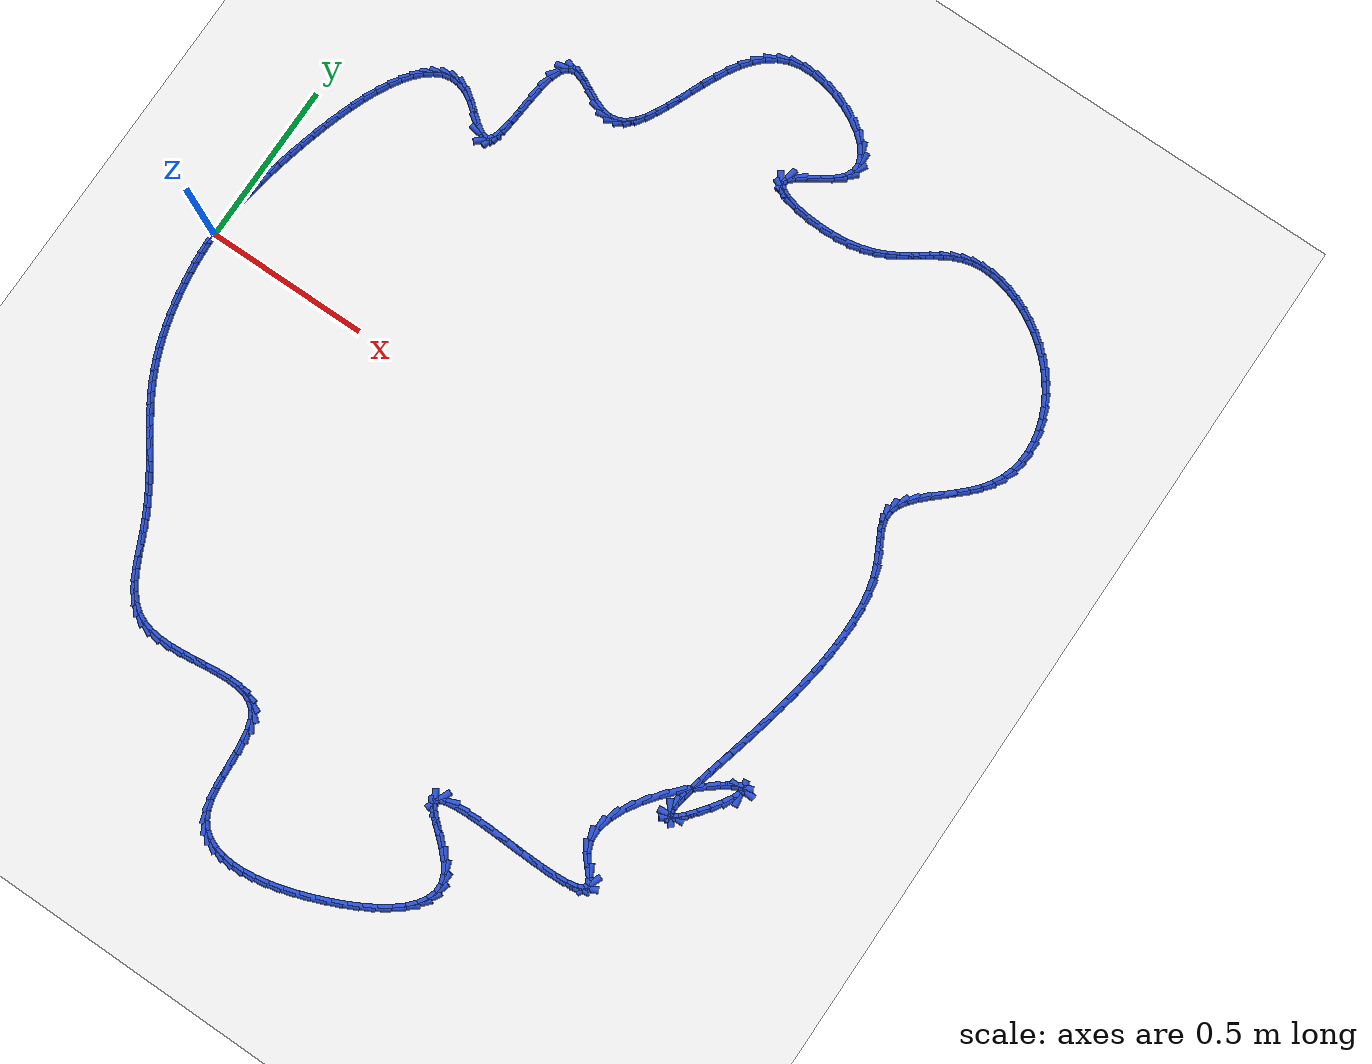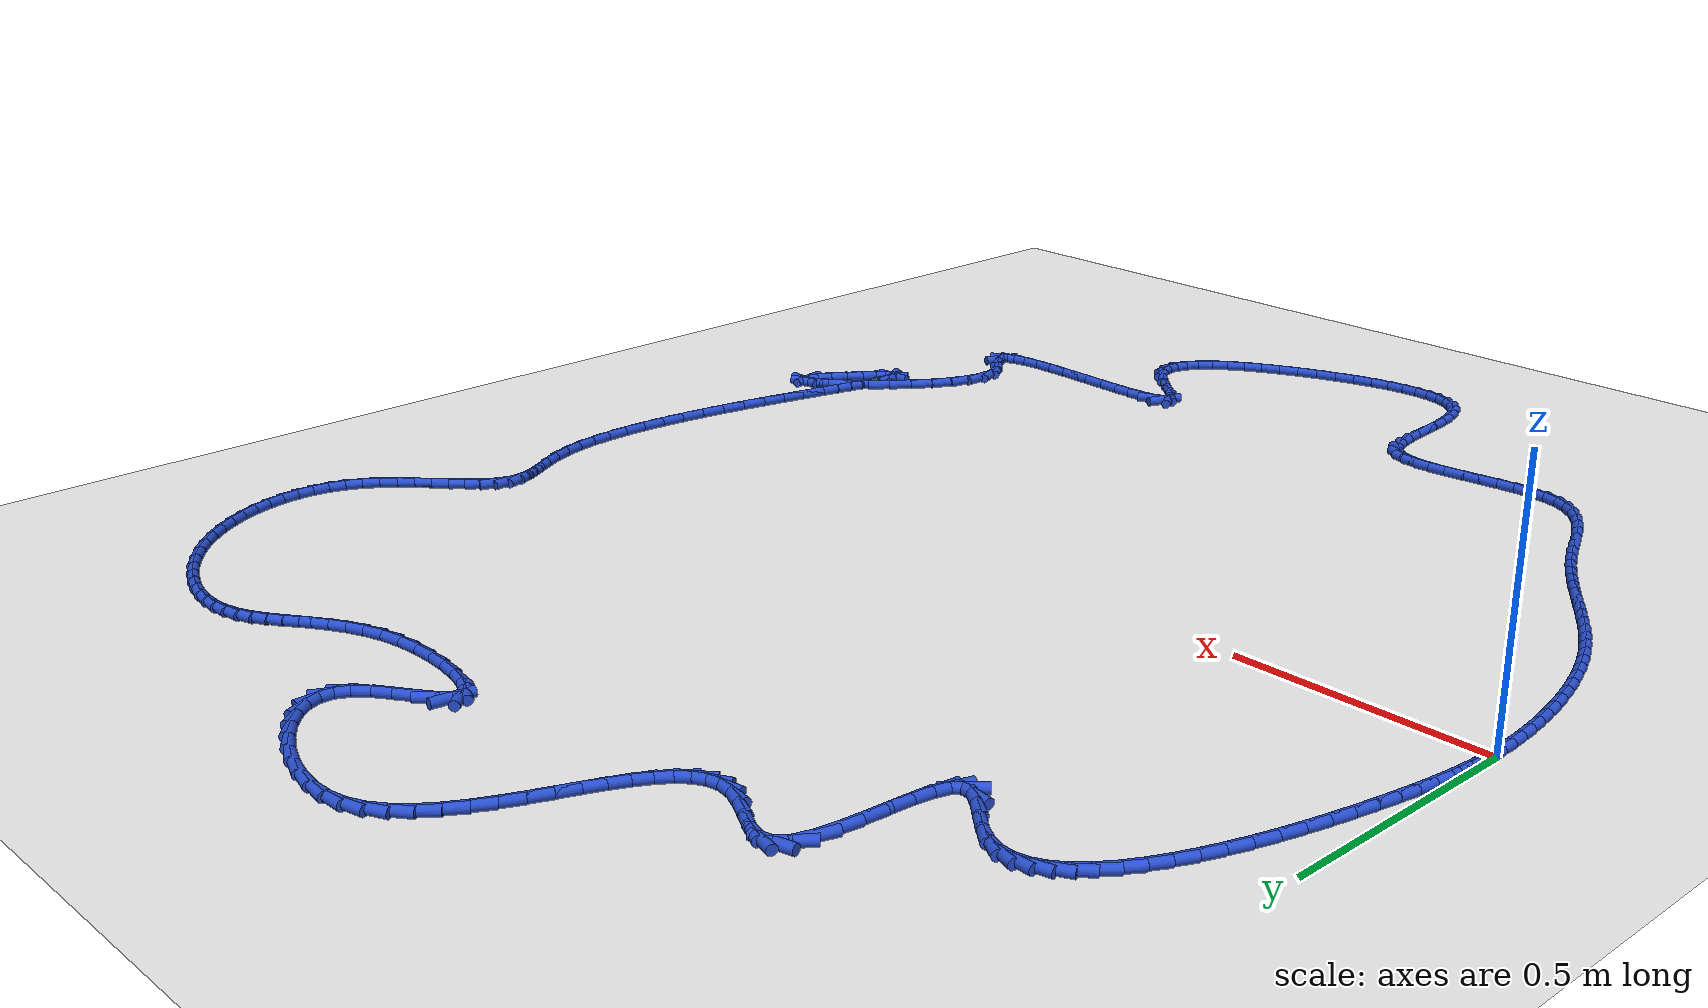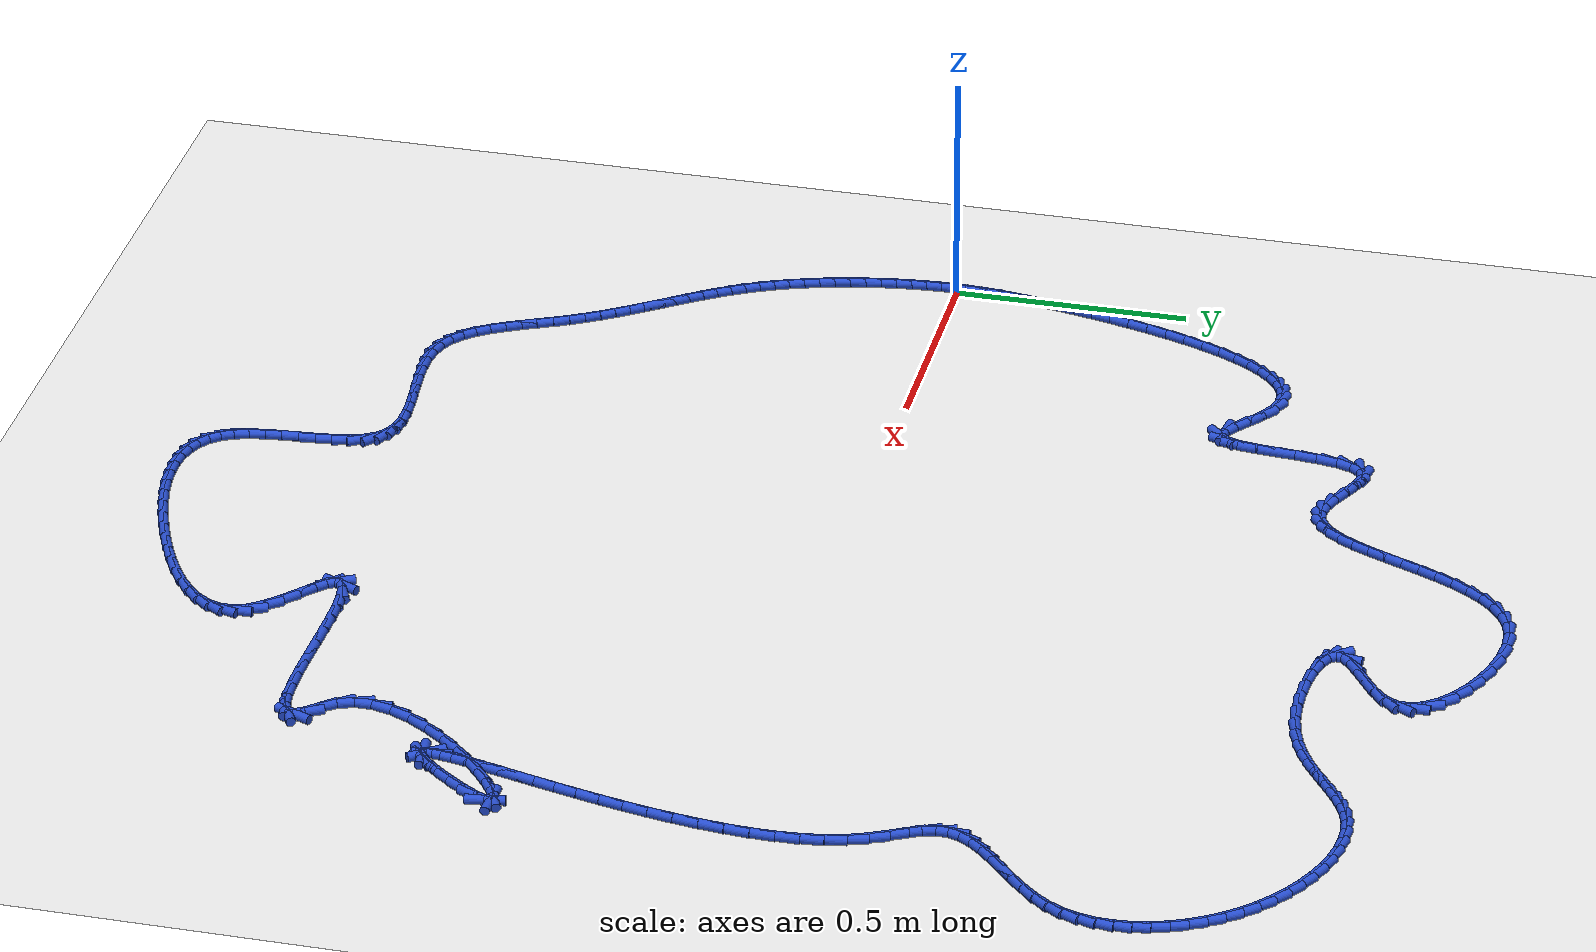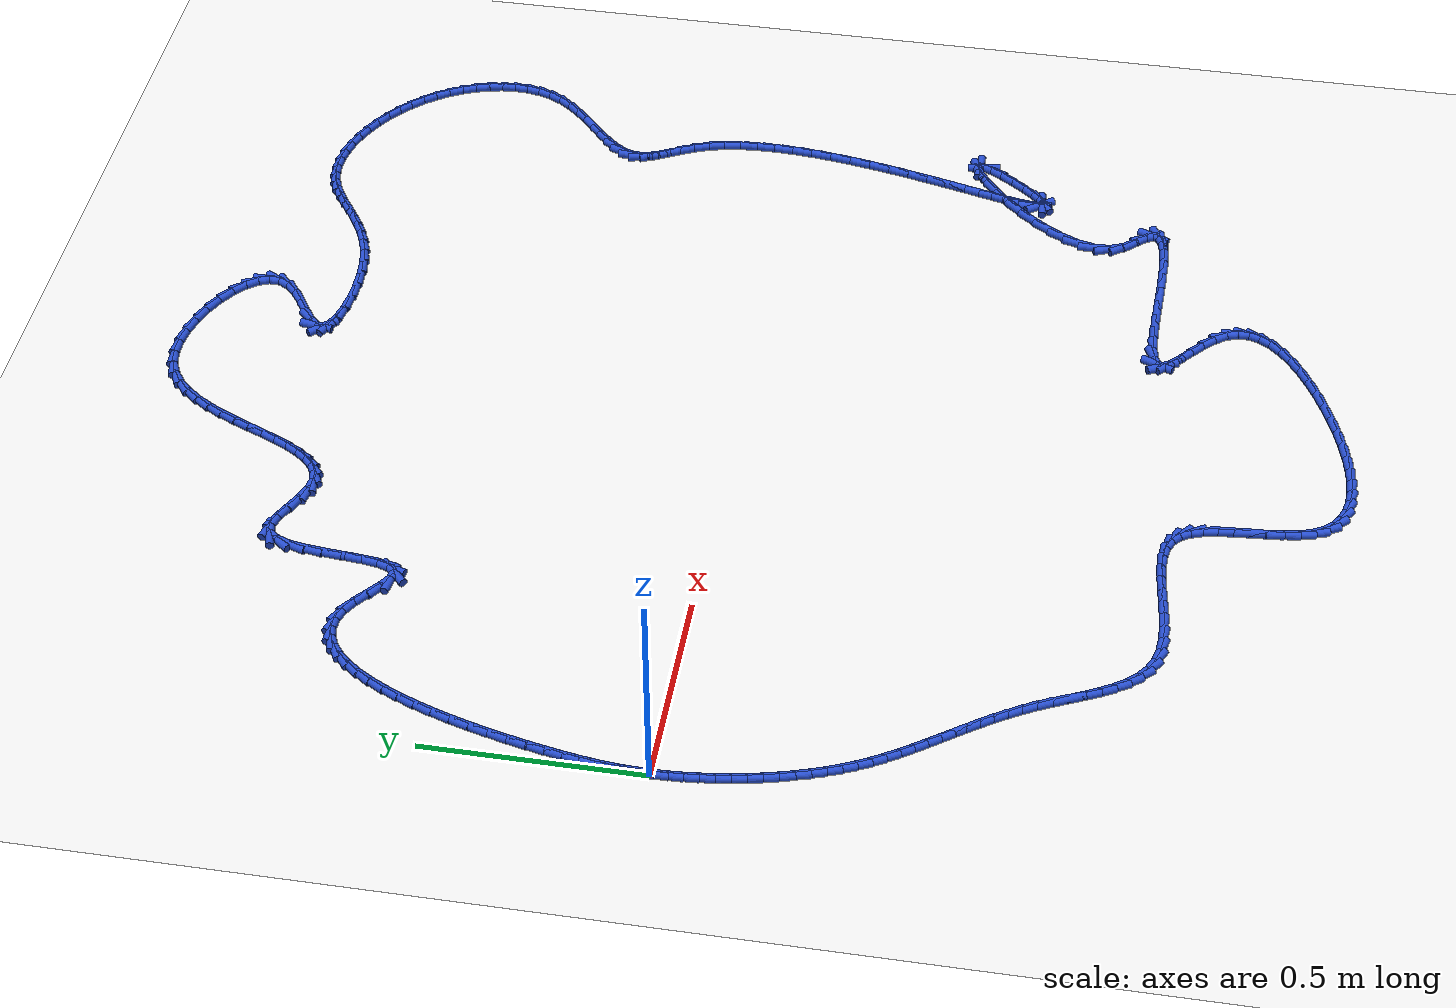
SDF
<sdf version="1.6">
 <world name="default">
  <light name="sun" type="directional">
   <pose>0 0 10 0 -0 0</pose>
   <diffuse>0.8 0.8 0.8 1</diffuse>
   <specular>0.2 0.2 0.2 1</specular>
   <attenuation>
    <range>1000</range>
    <constant>0.9</constant>
    <linear>0.01</linear>
    <quadratic>0.001</quadratic>
   </attenuation>
   <direction>-0.5 0.1 -0.9</direction>
  </light>
  <model name="ground_plane">
   <static>1</static>
   <link name="link">
    <collision name="collision">
     <geometry><plane><normal>0 0 1</normal><size>100 100</size></plane></geometry>
     <surface><friction><ode><mu>100</mu><mu2>50</mu2></ode></friction></surface>
    </collision>
    <visual name="visual">
     <cast_shadows>0</cast_shadows>
     <geometry><plane><normal>0 0 1</normal><size>100 100</size></plane></geometry>
     <material>
      <script><uri>file://media/materials/scripts/gazebo.material</uri><name>Gazebo/WhiteGlow</name></script>
     </material>
    </visual>
   </link>
  </model>
  <gravity>0 0 -9.8</gravity>
  <magnetic_field>6e-06 2.3e-05 -4.2e-05</magnetic_field>
  <atmosphere type="adiabatic"/>
  <physics name="default_physics" default="0" type="ode">
   <max_step_size>0.001</max_step_size>
   <real_time_factor>1</real_time_factor>
   <real_time_update_rate>1000</real_time_update_rate>
  </physics>
  <scene><ambient>0.4 0.4 0.4 1</ambient><background>0.7 0.7 0.7 1</background><shadows>1</shadows></scene>
  <spherical_coordinates>
   <surface_model>EARTH_WGS84</surface_model>
   <latitude_deg>0</latitude_deg>
   <longitude_deg>0</longitude_deg>
   <elevation>0</elevation>
   <heading_deg>0</heading_deg>
  </spherical_coordinates>
  <model name="line">
   <link name="link_0">
    <pose>-1.3010426069826053e-18 2.0816681711721685e-17 0.01 0 1.57 1.5551723138670699</pose>
    <collision name="collision">
     <geometry><cylinder><radius>0.01</radius><length>0.08</length></cylinder></geometry>
    </collision>
    <visual name="visual">
     <material>
      <script><name>Gazebo/Blue</name><uri>file://media/materials/scripts/gazebo.material</uri></script>
     </material>
     <geometry><cylinder><radius>0.01</radius><length>0.08</length></cylinder></geometry>
    </visual>
   </link>
   <link name="link_1">
    <pose>0.0004817022915168534 0.030828385576984422 0.01 0 1.57 1.5196772141333628</pose>
    <collision name="collision">
     <geometry><cylinder><radius>0.01</radius><length>0.08</length></cylinder></geometry>
    </collision>
    <visual name="visual">
     <material>
      <script><name>Gazebo/Blue</name><uri>file://media/materials/scripts/gazebo.material</uri></script>
     </material>
     <geometry><cylinder><radius>0.01</radius><length>0.08</length></cylinder></geometry>
    </visual>
   </link>
   <link name="link_2">
    <pose>0.002046395380871345 0.06141048760129893 0.01 0 1.57 1.4851034615570822</pose>
    <collision name="collision">
     <geometry><cylinder><radius>0.01</radius><length>0.08</length></cylinder></geometry>
    </collision>
    <visual name="visual">
     <material>
      <script><name>Gazebo/Blue</name><uri>file://media/materials/scripts/gazebo.material</uri></script>
     </material>
     <geometry><cylinder><radius>0.01</radius><length>0.08</length></cylinder></geometry>
    </visual>
   </link>
   <link name="link_3">
    <pose>0.004694872324788491 0.09224142009617421 0.01 0 1.57 1.4531140079023372</pose>
    <collision name="collision">
     <geometry><cylinder><radius>0.01</radius><length>0.08</length></cylinder></geometry>
    </collision>
    <visual name="visual">
     <material>
      <script><name>Gazebo/Blue</name><uri>file://media/materials/scripts/gazebo.material</uri></script>
     </material>
     <geometry><cylinder><radius>0.01</radius><length>0.08</length></cylinder></geometry>
    </visual>
   </link>
   <link name="link_4">
    <pose>0.008427926179993286 0.12381629708484068 0.01 0 1.57 1.4249975054829191</pose>
    <collision name="collision">
     <geometry><cylinder><radius>0.01</radius><length>0.08</length></cylinder></geometry>
    </collision>
    <visual name="visual">
     <material>
      <script><name>Gazebo/Blue</name><uri>file://media/materials/scripts/gazebo.material</uri></script>
     </material>
     <geometry><cylinder><radius>0.01</radius><length>0.08</length></cylinder></geometry>
    </visual>
   </link>
   <link name="link_5">
    <pose>0.013246350003210748 0.15663023259052902 0.01 0 1.57 1.4015227152400616</pose>
    <collision name="collision">
     <geometry><cylinder><radius>0.01</radius><length>0.08</length></cylinder></geometry>
    </collision>
    <visual name="visual">
     <material>
      <script><name>Gazebo/Blue</name><uri>file://media/materials/scripts/gazebo.material</uri></script>
     </material>
     <geometry><cylinder><radius>0.01</radius><length>0.08</length></cylinder></geometry>
    </visual>
   </link>
   <link name="link_6">
    <pose>0.019150936851165888 0.19117834063646985 0.01 0 1.57 1.3829308680715253</pose>
    <collision name="collision">
     <geometry><cylinder><radius>0.01</radius><length>0.08</length></cylinder></geometry>
    </collision>
    <visual name="visual">
     <material>
      <script><name>Gazebo/Blue</name><uri>file://media/materials/scripts/gazebo.material</uri></script>
     </material>
     <geometry><cylinder><radius>0.01</radius><length>0.08</length></cylinder></geometry>
    </visual>
   </link>
   <link name="link_7">
    <pose>0.026142483831508738 0.22795519654023153 0.01 0 1.57 1.3676389875326729</pose>
    <collision name="collision">
     <geometry><cylinder><radius>0.01</radius><length>0.08</length></cylinder></geometry>
    </collision>
    <visual name="visual">
     <material>
      <script><name>Gazebo/Blue</name><uri>file://media/materials/scripts/gazebo.material</uri></script>
     </material>
     <geometry><cylinder><radius>0.01</radius><length>0.08</length></cylinder></geometry>
    </visual>
   </link>
   <link name="link_8">
    <pose>0.034223820217309575 0.2671851314141515 0.01 0 1.57 1.3515767439560131</pose>
    <collision name="collision">
     <geometry><cylinder><radius>0.01</radius><length>0.08</length></cylinder></geometry>
    </collision>
    <visual name="visual">
     <material>
      <script><name>Gazebo/Blue</name><uri>file://media/materials/scripts/gazebo.material</uri></script>
     </material>
     <geometry><cylinder><radius>0.01</radius><length>0.08</length></cylinder></geometry>
    </visual>
   </link>
   <link name="link_9">
    <pose>0.043403097297997684 0.30838473670189154 0.01 0 1.57 1.333717444130101</pose>
    <collision name="collision">
     <geometry><cylinder><radius>0.01</radius><length>0.08</length></cylinder></geometry>
    </collision>
    <visual name="visual">
     <material>
      <script><name>Gazebo/Blue</name><uri>file://media/materials/scripts/gazebo.material</uri></script>
     </material>
     <geometry><cylinder><radius>0.01</radius><length>0.08</length></cylinder></geometry>
    </visual>
   </link>
   <link name="link_10">
    <pose>0.05368932692404109 0.3509561635404214 0.01 0 1.57 1.313569493242332</pose>
    <collision name="collision">
     <geometry><cylinder><radius>0.01</radius><length>0.08</length></cylinder></geometry>
    </collision>
    <visual name="visual">
     <material>
      <script><name>Gazebo/Blue</name><uri>file://media/materials/scripts/gazebo.material</uri></script>
     </material>
     <geometry><cylinder><radius>0.01</radius><length>0.08</length></cylinder></geometry>
    </visual>
   </link>
   <link name="link_11">
    <pose>0.06509152094590767 0.3943015630667108 0.01 0 1.57 1.2905338697243343</pose>
    <collision name="collision">
     <geometry><cylinder><radius>0.01</radius><length>0.08</length></cylinder></geometry>
    </collision>
    <visual name="visual">
     <material>
      <script><name>Gazebo/Blue</name><uri>file://media/materials/scripts/gazebo.material</uri></script>
     </material>
     <geometry><cylinder><radius>0.01</radius><length>0.08</length></cylinder></geometry>
    </visual>
   </link>
   <link name="link_12">
    <pose>0.07761869121406546 0.4378230864177297 0.01 0 1.57 1.2638482378023026</pose>
    <collision name="collision">
     <geometry><cylinder><radius>0.01</radius><length>0.08</length></cylinder></geometry>
    </collision>
    <visual name="visual">
     <material>
      <script><name>Gazebo/Blue</name><uri>file://media/materials/scripts/gazebo.material</uri></script>
     </material>
     <geometry><cylinder><radius>0.01</radius><length>0.08</length></cylinder></geometry>
    </visual>
   </link>
   <link name="link_13">
    <pose>0.09127984957898234 0.4809228847304477 0.01 0 1.57 1.232511752893902</pose>
    <collision name="collision">
     <geometry><cylinder><radius>0.01</radius><length>0.08</length></cylinder></geometry>
    </collision>
    <visual name="visual">
     <material>
      <script><name>Gazebo/Blue</name><uri>file://media/materials/scripts/gazebo.material</uri></script>
     </material>
     <geometry><cylinder><radius>0.01</radius><length>0.08</length></cylinder></geometry>
    </visual>
   </link>
   <link name="link_14">
    <pose>0.1060840078911263 0.5230031091418346 0.01 0 1.57 1.1951772889500376</pose>
    <collision name="collision">
     <geometry><cylinder><radius>0.01</radius><length>0.08</length></cylinder></geometry>
    </collision>
    <visual name="visual">
     <material>
      <script><name>Gazebo/Blue</name><uri>file://media/materials/scripts/gazebo.material</uri></script>
     </material>
     <geometry><cylinder><radius>0.01</radius><length>0.08</length></cylinder></geometry>
    </visual>
   </link>
   <link name="link_15">
    <pose>0.12204017800096531 0.5634659107888601 0.01 0 1.57 1.1499923260401879</pose>
    <collision name="collision">
     <geometry><cylinder><radius>0.01</radius><length>0.08</length></cylinder></geometry>
    </collision>
    <visual name="visual">
     <material>
      <script><name>Gazebo/Blue</name><uri>file://media/materials/scripts/gazebo.material</uri></script>
     </material>
     <geometry><cylinder><radius>0.01</radius><length>0.08</length></cylinder></geometry>
    </visual>
   </link>
   <link name="link_16">
    <pose>0.1391573717589673 0.6017134408084943 0.01 0 1.57 1.0943622958399073</pose>
    <collision name="collision">
     <geometry><cylinder><radius>0.01</radius><length>0.08</length></cylinder></geometry>
    </collision>
    <visual name="visual">
     <material>
      <script><name>Gazebo/Blue</name><uri>file://media/materials/scripts/gazebo.material</uri></script>
     </material>
     <geometry><cylinder><radius>0.01</radius><length>0.08</length></cylinder></geometry>
    </visual>
   </link>
   <link name="link_17">
    <pose>0.15744460101560026 0.6371478503377068 0.01 0 1.57 1.0246058608984216</pose>
    <collision name="collision">
     <geometry><cylinder><radius>0.01</radius><length>0.08</length></cylinder></geometry>
    </collision>
    <visual name="visual">
     <material>
      <script><name>Gazebo/Blue</name><uri>file://media/materials/scripts/gazebo.material</uri></script>
     </material>
     <geometry><cylinder><radius>0.01</radius><length>0.08</length></cylinder></geometry>
    </visual>
   </link>
   <link name="link_18">
    <pose>0.1769108776213321 0.6691712905134674 0.01 0 1.57 0.9354924277948665</pose>
    <collision name="collision">
     <geometry><cylinder><radius>0.01</radius><length>0.08</length></cylinder></geometry>
    </collision>
    <visual name="visual">
     <material>
      <script><name>Gazebo/Blue</name><uri>file://media/materials/scripts/gazebo.material</uri></script>
     </material>
     <geometry><cylinder><radius>0.01</radius><length>0.08</length></cylinder></geometry>
    </visual>
   </link>
   <link name="link_19">
    <pose>0.19756521342663086 0.6971859124727459 0.01 0 1.57 0.8197763496850885</pose>
    <collision name="collision">
     <geometry><cylinder><radius>0.01</radius><length>0.08</length></cylinder></geometry>
    </collision>
    <visual name="visual">
     <material>
      <script><name>Gazebo/Blue</name><uri>file://media/materials/scripts/gazebo.material</uri></script>
     </material>
     <geometry><cylinder><radius>0.01</radius><length>0.08</length></cylinder></geometry>
    </visual>
   </link>
   <link name="link_20">
    <pose>0.21941662028196435 0.7205938673525119 0.01 0 1.57 0.6682936282033193</pose>
    <collision name="collision">
     <geometry><cylinder><radius>0.01</radius><length>0.08</length></cylinder></geometry>
    </collision>
    <visual name="visual">
     <material>
      <script><name>Gazebo/Blue</name><uri>file://media/materials/scripts/gazebo.material</uri></script>
     </material>
     <geometry><cylinder><radius>0.01</radius><length>0.08</length></cylinder></geometry>
    </visual>
   </link>
   <link name="link_21">
    <pose>0.24247411003780062 0.7387973062897352 0.01 0 1.57 0.4723364206903863</pose>
    <collision name="collision">
     <geometry><cylinder><radius>0.01</radius><length>0.08</length></cylinder></geometry>
    </collision>
    <visual name="visual">
     <material>
      <script><name>Gazebo/Blue</name><uri>file://media/materials/scripts/gazebo.material</uri></script>
     </material>
     <geometry><cylinder><radius>0.01</radius><length>0.08</length></cylinder></geometry>
    </visual>
   </link>
   <link name="link_22">
    <pose>0.2667466945446077 0.7511983804213861 0.01 0 1.57 0.2311515779181811</pose>
    <collision name="collision">
     <geometry><cylinder><radius>0.01</radius><length>0.08</length></cylinder></geometry>
    </collision>
    <visual name="visual">
     <material>
      <script><name>Gazebo/Blue</name><uri>file://media/materials/scripts/gazebo.material</uri></script>
     </material>
     <geometry><cylinder><radius>0.01</radius><length>0.08</length></cylinder></geometry>
    </visual>
   </link>
   <link name="link_23">
    <pose>0.2922433856528534 0.7571992408844337 0.01 0 1.57 -0.03728944717608976</pose>
    <collision name="collision">
     <geometry><cylinder><radius>0.01</radius><length>0.08</length></cylinder></geometry>
    </collision>
    <visual name="visual">
     <material>
      <script><name>Gazebo/Blue</name><uri>file://media/materials/scripts/gazebo.material</uri></script>
     </material>
     <geometry><cylinder><radius>0.01</radius><length>0.08</length></cylinder></geometry>
    </visual>
   </link>
   <link name="link_24">
    <pose>0.3189731952130057 0.7562020388158484 0.01 0 1.57 -0.29805350194099717</pose>
    <collision name="collision">
     <geometry><cylinder><radius>0.01</radius><length>0.08</length></cylinder></geometry>
    </collision>
    <visual name="visual">
     <material>
      <script><name>Gazebo/Blue</name><uri>file://media/materials/scripts/gazebo.material</uri></script>
     </material>
     <geometry><cylinder><radius>0.01</radius><length>0.08</length></cylinder></geometry>
    </visual>
   </link>
   <link name="link_25">
    <pose>0.34694513507553276 0.7476089253525995 0.01 0 1.57 -0.5210832161069502</pose>
    <collision name="collision">
     <geometry><cylinder><radius>0.01</radius><length>0.08</length></cylinder></geometry>
    </collision>
    <visual name="visual">
     <material>
      <script><name>Gazebo/Blue</name><uri>file://media/materials/scripts/gazebo.material</uri></script>
     </material>
     <geometry><cylinder><radius>0.01</radius><length>0.08</length></cylinder></geometry>
    </visual>
   </link>
   <link name="link_26">
    <pose>0.37616404134145554 0.7308372425615483 0.01 0 1.57 -0.6617652204785025</pose>
    <collision name="collision">
     <geometry><cylinder><radius>0.01</radius><length>0.08</length></cylinder></geometry>
    </collision>
    <visual name="visual">
     <material>
      <script><name>Gazebo/Blue</name><uri>file://media/materials/scripts/gazebo.material</uri></script>
     </material>
     <geometry><cylinder><radius>0.01</radius><length>0.08</length></cylinder></geometry>
    </visual>
   </link>
   <link name="link_27">
    <pose>0.4060058005009487 0.7075923839278063 0.01 0 1.57 -0.6846321859253136</pose>
    <collision name="collision">
     <geometry><cylinder><radius>0.01</radius><length>0.08</length></cylinder></geometry>
    </collision>
    <visual name="visual">
     <material>
      <script><name>Gazebo/Blue</name><uri>file://media/materials/scripts/gazebo.material</uri></script>
     </material>
     <geometry><cylinder><radius>0.01</radius><length>0.08</length></cylinder></geometry>
    </visual>
   </link>
   <link name="link_28">
    <pose>0.4345518635776319 0.6842887607242489 0.01 0 1.57 -0.576540801429091</pose>
    <collision name="collision">
     <geometry><cylinder><radius>0.01</radius><length>0.08</length></cylinder></geometry>
    </collision>
    <visual name="visual">
     <material>
      <script><name>Gazebo/Blue</name><uri>file://media/materials/scripts/gazebo.material</uri></script>
     </material>
     <geometry><cylinder><radius>0.01</radius><length>0.08</length></cylinder></geometry>
    </visual>
   </link>
   <link name="link_29">
    <pose>0.45972424982475063 0.6679207799531796 0.01 0 1.57 -0.12818487885726956</pose>
    <collision name="collision">
     <geometry><cylinder><radius>0.01</radius><length>0.08</length></cylinder></geometry>
    </collision>
    <visual name="visual">
     <material>
      <script><name>Gazebo/Blue</name><uri>file://media/materials/scripts/gazebo.material</uri></script>
     </material>
     <geometry><cylinder><radius>0.01</radius><length>0.08</length></cylinder></geometry>
    </visual>
   </link>
   <link name="link_30">
    <pose>0.47948115888364623 0.6653742801689198 0.01 0 1.57 0.7882257571373025</pose>
    <collision name="collision">
     <geometry><cylinder><radius>0.01</radius><length>0.08</length></cylinder></geometry>
    </collision>
    <visual name="visual">
     <material>
      <script><name>Gazebo/Blue</name><uri>file://media/materials/scripts/gazebo.material</uri></script>
     </material>
     <geometry><cylinder><radius>0.01</radius><length>0.08</length></cylinder></geometry>
    </visual>
   </link>
   <link name="link_31">
    <pose>0.4932263269047279 0.6791974003167964 0.01 0 1.57 1.2482002838909911</pose>
    <collision name="collision">
     <geometry><cylinder><radius>0.01</radius><length>0.08</length></cylinder></geometry>
    </collision>
    <visual name="visual">
     <material>
      <script><name>Gazebo/Blue</name><uri>file://media/materials/scripts/gazebo.material</uri></script>
     </material>
     <geometry><cylinder><radius>0.01</radius><length>0.08</length></cylinder></geometry>
    </visual>
   </link>
   <link name="link_32">
    <pose>0.502264186214137 0.706234757496399 0.01 0 1.57 1.4150362834357857</pose>
    <collision name="collision">
     <geometry><cylinder><radius>0.01</radius><length>0.08</length></cylinder></geometry>
    </collision>
    <visual name="visual">
     <material>
      <script><name>Gazebo/Blue</name><uri>file://media/materials/scripts/gazebo.material</uri></script>
     </material>
     <geometry><cylinder><radius>0.01</radius><length>0.08</length></cylinder></geometry>
    </visual>
   </link>
   <link name="link_33">
    <pose>0.5080285251550136 0.7429428032087051 0.01 0 1.57 1.4794303102696176</pose>
    <collision name="collision">
     <geometry><cylinder><radius>0.01</radius><length>0.08</length></cylinder></geometry>
    </collision>
    <visual name="visual">
     <material>
      <script><name>Gazebo/Blue</name><uri>file://media/materials/scripts/gazebo.material</uri></script>
     </material>
     <geometry><cylinder><radius>0.01</radius><length>0.08</length></cylinder></geometry>
    </visual>
   </link>
   <link name="link_34">
    <pose>0.5119531320704979 0.7857779889546928 0.01 0 1.57 1.493479208219994</pose>
    <collision name="collision">
     <geometry><cylinder><radius>0.01</radius><length>0.08</length></cylinder></geometry>
    </collision>
    <visual name="visual">
     <material>
      <script><name>Gazebo/Blue</name><uri>file://media/materials/scripts/gazebo.material</uri></script>
     </material>
     <geometry><cylinder><radius>0.01</radius><length>0.08</length></cylinder></geometry>
    </visual>
   </link>
   <link name="link_35">
    <pose>0.5154717953037297 0.8311967662353396 0.01 0 1.57 1.4688872397158814</pose>
    <collision name="collision">
     <geometry><cylinder><radius>0.01</radius><length>0.08</length></cylinder></geometry>
    </collision>
    <visual name="visual">
     <material>
      <script><name>Gazebo/Blue</name><uri>file://media/materials/scripts/gazebo.material</uri></script>
     </material>
     <geometry><cylinder><radius>0.01</radius><length>0.08</length></cylinder></geometry>
    </visual>
   </link>
   <link name="link_36">
    <pose>0.5200183031978493 0.8756555865516232 0.01 0 1.57 1.397163090553568</pose>
    <collision name="collision">
     <geometry><cylinder><radius>0.01</radius><length>0.08</length></cylinder></geometry>
    </collision>
    <visual name="visual">
     <material>
      <script><name>Gazebo/Blue</name><uri>file://media/materials/scripts/gazebo.material</uri></script>
     </material>
     <geometry><cylinder><radius>0.01</radius><length>0.08</length></cylinder></geometry>
    </visual>
   </link>
   <link name="link_37">
    <pose>0.5270264440959967 0.9156109014045218 0.01 0 1.57 1.2415204685135708</pose>
    <collision name="collision">
     <geometry><cylinder><radius>0.01</radius><length>0.08</length></cylinder></geometry>
    </collision>
    <visual name="visual">
     <material>
      <script><name>Gazebo/Blue</name><uri>file://media/materials/scripts/gazebo.material</uri></script>
     </material>
     <geometry><cylinder><radius>0.01</radius><length>0.08</length></cylinder></geometry>
    </visual>
   </link>
   <link name="link_38">
    <pose>0.5379300063413122 0.9475191622950129 0.01 0 1.57 0.8966965953635448</pose>
    <collision name="collision">
     <geometry><cylinder><radius>0.01</radius><length>0.08</length></cylinder></geometry>
    </collision>
    <visual name="visual">
     <material>
      <script><name>Gazebo/Blue</name><uri>file://media/materials/scripts/gazebo.material</uri></script>
     </material>
     <geometry><cylinder><radius>0.01</radius><length>0.08</length></cylinder></geometry>
    </visual>
   </link>
   <link name="link_39">
    <pose>0.5541627782769359 0.9678368207240746 0.01 0 1.57 0.23488260720719853</pose>
    <collision name="collision">
     <geometry><cylinder><radius>0.01</radius><length>0.08</length></cylinder></geometry>
    </collision>
    <visual name="visual">
     <material>
      <script><name>Gazebo/Blue</name><uri>file://media/materials/scripts/gazebo.material</uri></script>
     </material>
     <geometry><cylinder><radius>0.01</radius><length>0.08</length></cylinder></geometry>
    </visual>
   </link>
   <link name="link_40">
    <pose>0.577037416481246 0.9733107121537168 0.01 0 1.57 -0.26231255431478334</pose>
    <collision name="collision">
     <geometry><cylinder><radius>0.01</radius><length>0.08</length></cylinder></geometry>
    </collision>
    <visual name="visual">
     <material>
      <script><name>Gazebo/Blue</name><uri>file://media/materials/scripts/gazebo.material</uri></script>
     </material>
     <geometry><cylinder><radius>0.01</radius><length>0.08</length></cylinder></geometry>
    </visual>
   </link>
   <link name="link_41">
    <pose>0.6058252776995768 0.9655811921918901 0.01 0 1.57 -0.4407397280460852</pose>
    <collision name="collision">
     <geometry><cylinder><radius>0.01</radius><length>0.08</length></cylinder></geometry>
    </collision>
    <visual name="visual">
     <material>
      <script><name>Gazebo/Blue</name><uri>file://media/materials/scripts/gazebo.material</uri></script>
     </material>
     <geometry><cylinder><radius>0.01</radius><length>0.08</length></cylinder></geometry>
    </visual>
   </link>
   <link name="link_42">
    <pose>0.6381004045423657 0.9503575144979994 0.01 0 1.57 -0.4694582988560868</pose>
    <collision name="collision">
     <geometry><cylinder><radius>0.01</radius><length>0.08</length></cylinder></geometry>
    </collision>
    <visual name="visual">
     <material>
      <script><name>Gazebo/Blue</name><uri>file://media/materials/scripts/gazebo.material</uri></script>
     </material>
     <geometry><cylinder><radius>0.01</radius><length>0.08</length></cylinder></geometry>
    </visual>
   </link>
   <link name="link_43">
    <pose>0.6713852402683699 0.933472629634216 0.01 0 1.57 -0.38014816157834924</pose>
    <collision name="collision">
     <geometry><cylinder><radius>0.01</radius><length>0.08</length></cylinder></geometry>
    </collision>
    <visual name="visual">
     <material>
      <script><name>Gazebo/Blue</name><uri>file://media/materials/scripts/gazebo.material</uri></script>
     </material>
     <geometry><cylinder><radius>0.01</radius><length>0.08</length></cylinder></geometry>
    </visual>
   </link>
   <link name="link_44">
    <pose>0.7032024556235295 0.9207589626067163 0.01 0 1.57 -0.14386166004241532</pose>
    <collision name="collision">
     <geometry><cylinder><radius>0.01</radius><length>0.08</length></cylinder></geometry>
    </collision>
    <visual name="visual">
     <material>
      <script><name>Gazebo/Blue</name><uri>file://media/materials/scripts/gazebo.material</uri></script>
     </material>
     <geometry><cylinder><radius>0.01</radius><length>0.08</length></cylinder></geometry>
    </visual>
   </link>
   <link name="link_45">
    <pose>0.7316878260420713 0.9166325032648772 0.01 0 1.57 0.17179562194703762</pose>
    <collision name="collision">
     <geometry><cylinder><radius>0.01</radius><length>0.08</length></cylinder></geometry>
    </collision>
    <visual name="visual">
     <material>
      <script><name>Gazebo/Blue</name><uri>file://media/materials/scripts/gazebo.material</uri></script>
     </material>
     <geometry><cylinder><radius>0.01</radius><length>0.08</length></cylinder></geometry>
    </visual>
   </link>
   <link name="link_46">
    <pose>0.756924127669796 0.9210111511467897 0.01 0 1.57 0.4876830210978018</pose>
    <collision name="collision">
     <geometry><cylinder><radius>0.01</radius><length>0.08</length></cylinder></geometry>
    </collision>
    <visual name="visual">
     <material>
      <script><name>Gazebo/Blue</name><uri>file://media/materials/scripts/gazebo.material</uri></script>
     </material>
     <geometry><cylinder><radius>0.01</radius><length>0.08</length></cylinder></geometry>
    </visual>
   </link>
   <link name="link_47">
    <pose>0.7793797400025937 0.9329219593297636 0.01 0 1.57 0.742090968433786</pose>
    <collision name="collision">
     <geometry><cylinder><radius>0.01</radius><length>0.08</length></cylinder></geometry>
    </collision>
    <visual name="visual">
     <material>
      <script><name>Gazebo/Blue</name><uri>file://media/materials/scripts/gazebo.material</uri></script>
     </material>
     <geometry><cylinder><radius>0.01</radius><length>0.08</length></cylinder></geometry>
    </visual>
   </link>
   <link name="link_48">
    <pose>0.7995230425363558 0.9513919808911093 0.01 0 1.57 0.9204887943762573</pose>
    <collision name="collision">
     <geometry><cylinder><radius>0.01</radius><length>0.08</length></cylinder></geometry>
    </collision>
    <visual name="visual">
     <material>
      <script><name>Gazebo/Blue</name><uri>file://media/materials/scripts/gazebo.material</uri></script>
     </material>
     <geometry><cylinder><radius>0.01</radius><length>0.08</length></cylinder></geometry>
    </visual>
   </link>
   <link name="link_49">
    <pose>0.8178224147669724 0.9754482689081369 0.01 0 1.57 1.037535776436462</pose>
    <collision name="collision">
     <geometry><cylinder><radius>0.01</radius><length>0.08</length></cylinder></geometry>
    </collision>
    <visual name="visual">
     <material>
      <script><name>Gazebo/Blue</name><uri>file://media/materials/scripts/gazebo.material</uri></script>
     </material>
     <geometry><cylinder><radius>0.01</radius><length>0.08</length></cylinder></geometry>
    </visual>
   </link>
   <link name="link_50">
    <pose>0.8347462361903344 1.0041178764581569 0.01 0 1.57 1.110579899351142</pose>
    <collision name="collision">
     <geometry><cylinder><radius>0.01</radius><length>0.08</length></cylinder></geometry>
    </collision>
    <visual name="visual">
     <material>
      <script><name>Gazebo/Blue</name><uri>file://media/materials/scripts/gazebo.material</uri></script>
     </material>
     <geometry><cylinder><radius>0.01</radius><length>0.08</length></cylinder></geometry>
    </visual>
   </link>
   <link name="link_51">
    <pose>0.8507628863023329 1.0364278566184792 0.01 0 1.57 1.151800066752981</pose>
    <collision name="collision">
     <geometry><cylinder><radius>0.01</radius><length>0.08</length></cylinder></geometry>
    </collision>
    <visual name="visual">
     <material>
      <script><name>Gazebo/Blue</name><uri>file://media/materials/scripts/gazebo.material</uri></script>
     </material>
     <geometry><cylinder><radius>0.01</radius><length>0.08</length></cylinder></geometry>
    </visual>
   </link>
   <link name="link_52">
    <pose>0.8663407445988583 1.0714052624664145 0.01 0 1.57 1.1684200797756157</pose>
    <collision name="collision">
     <geometry><cylinder><radius>0.01</radius><length>0.08</length></cylinder></geometry>
    </collision>
    <visual name="visual">
     <material>
      <script><name>Gazebo/Blue</name><uri>file://media/materials/scripts/gazebo.material</uri></script>
     </material>
     <geometry><cylinder><radius>0.01</radius><length>0.08</length></cylinder></geometry>
    </visual>
   </link>
   <link name="link_53">
    <pose>0.8819481905758014 1.1080771470792725 0.01 0 1.57 1.164106102001867</pose>
    <collision name="collision">
     <geometry><cylinder><radius>0.01</radius><length>0.08</length></cylinder></geometry>
    </collision>
    <visual name="visual">
     <material>
      <script><name>Gazebo/Blue</name><uri>file://media/materials/scripts/gazebo.material</uri></script>
     </material>
     <geometry><cylinder><radius>0.01</radius><length>0.08</length></cylinder></geometry>
    </visual>
   </link>
   <link name="link_54">
    <pose>0.8980536037290531 1.1454705635343634 0.01 0 1.57 1.1399589707452333</pose>
    <collision name="collision">
     <geometry><cylinder><radius>0.01</radius><length>0.08</length></cylinder></geometry>
    </collision>
    <visual name="visual">
     <material>
      <script><name>Gazebo/Blue</name><uri>file://media/materials/scripts/gazebo.material</uri></script>
     </material>
     <geometry><cylinder><radius>0.01</radius><length>0.08</length></cylinder></geometry>
    </visual>
   </link>
   <link name="link_55">
    <pose>0.915125363554504 1.182612564908998 0.01 0 1.57 1.0950249901635338</pose>
    <collision name="collision">
     <geometry><cylinder><radius>0.01</radius><length>0.08</length></cylinder></geometry>
    </collision>
    <visual name="visual">
     <material>
      <script><name>Gazebo/Blue</name><uri>file://media/materials/scripts/gazebo.material</uri></script>
     </material>
     <geometry><cylinder><radius>0.01</radius><length>0.08</length></cylinder></geometry>
    </visual>
   </link>
   <link name="link_56">
    <pose>0.9336318495480446 1.2185302042804858 0.01 0 1.57 1.0265176223357433</pose>
    <collision name="collision">
     <geometry><cylinder><radius>0.01</radius><length>0.08</length></cylinder></geometry>
    </collision>
    <visual name="visual">
     <material>
      <script><name>Gazebo/Blue</name><uri>file://media/materials/scripts/gazebo.material</uri></script>
     </material>
     <geometry><cylinder><radius>0.01</radius><length>0.08</length></cylinder></geometry>
    </visual>
   </link>
   <link name="link_57">
    <pose>0.9540414412055662 1.2522505347261375 0.01 0 1.57 0.9300552969689843</pose>
    <collision name="collision">
     <geometry><cylinder><radius>0.01</radius><length>0.08</length></cylinder></geometry>
    </collision>
    <visual name="visual">
     <material>
      <script><name>Gazebo/Blue</name><uri>file://media/materials/scripts/gazebo.material</uri></script>
     </material>
     <geometry><cylinder><radius>0.01</radius><length>0.08</length></cylinder></geometry>
    </visual>
   </link>
   <link name="link_58">
    <pose>0.976822518022959 1.2828006093232633 0.01 0 1.57 0.8005029800440301</pose>
    <collision name="collision">
     <geometry><cylinder><radius>0.01</radius><length>0.08</length></cylinder></geometry>
    </collision>
    <visual name="visual">
     <material>
      <script><name>Gazebo/Blue</name><uri>file://media/materials/scripts/gazebo.material</uri></script>
     </material>
     <geometry><cylinder><radius>0.01</radius><length>0.08</length></cylinder></geometry>
    </visual>
   </link>
   <link name="link_59">
    <pose>1.0024434594961145 1.3092074811491734 0.01 0 1.57 0.6344547593436728</pose>
    <collision name="collision">
     <geometry><cylinder><radius>0.01</radius><length>0.08</length></cylinder></geometry>
    </collision>
    <visual name="visual">
     <material>
      <script><name>Gazebo/Blue</name><uri>file://media/materials/scripts/gazebo.material</uri></script>
     </material>
     <geometry><cylinder><radius>0.01</radius><length>0.08</length></cylinder></geometry>
    </visual>
   </link>
   <link name="link_60">
    <pose>1.0313726451209222 1.3304982032811776 0.01 0 1.57 0.4350923461939201</pose>
    <collision name="collision">
     <geometry><cylinder><radius>0.01</radius><length>0.08</length></cylinder></geometry>
    </collision>
    <visual name="visual">
     <material>
      <script><name>Gazebo/Blue</name><uri>file://media/materials/scripts/gazebo.material</uri></script>
     </material>
     <geometry><cylinder><radius>0.01</radius><length>0.08</length></cylinder></geometry>
    </visual>
   </link>
   <link name="link_61">
    <pose>1.064078454393274 1.3456998287965865 0.01 0 1.57 0.21811525118055394</pose>
    <collision name="collision">
     <geometry><cylinder><radius>0.01</radius><length>0.08</length></cylinder></geometry>
    </collision>
    <visual name="visual">
     <material>
      <script><name>Gazebo/Blue</name><uri>file://media/materials/scripts/gazebo.material</uri></script>
     </material>
     <geometry><cylinder><radius>0.01</radius><length>0.08</length></cylinder></geometry>
    </visual>
   </link>
   <link name="link_62">
    <pose>1.1009821249991096 1.3538792047008816 0.01 0 1.57 0.026943637637133318</pose>
    <collision name="collision">
     <geometry><cylinder><radius>0.01</radius><length>0.08</length></cylinder></geometry>
    </collision>
    <visual name="visual">
     <material>
      <script><name>Gazebo/Blue</name><uri>file://media/materials/scripts/gazebo.material</uri></script>
     </material>
     <geometry><cylinder><radius>0.01</radius><length>0.08</length></cylinder></geometry>
    </visual>
   </link>
   <link name="link_63">
    <pose>1.141477354836255 1.3549705576051376 0.01 0 1.57 -0.12227832996808444</pose>
    <collision name="collision">
     <geometry><cylinder><radius>0.01</radius><length>0.08</length></cylinder></geometry>
    </collision>
    <visual name="visual">
     <material>
      <script><name>Gazebo/Blue</name><uri>file://media/materials/scripts/gazebo.material</uri></script>
     </material>
     <geometry><cylinder><radius>0.01</radius><length>0.08</length></cylinder></geometry>
    </visual>
   </link>
   <link name="link_64">
    <pose>1.183960859882995 1.3497496988397337 0.01 0 1.57 -0.24532494615522302</pose>
    <collision name="collision">
     <geometry><cylinder><radius>0.01</radius><length>0.08</length></cylinder></geometry>
    </collision>
    <visual name="visual">
     <material>
      <script><name>Gazebo/Blue</name><uri>file://media/materials/scripts/gazebo.material</uri></script>
     </material>
     <geometry><cylinder><radius>0.01</radius><length>0.08</length></cylinder></geometry>
    </visual>
   </link>
   <link name="link_65">
    <pose>1.2267883276276228 1.3390270732119007 0.01 0 1.57 -0.3554155689781578</pose>
    <collision name="collision">
     <geometry><cylinder><radius>0.01</radius><length>0.08</length></cylinder></geometry>
    </collision>
    <visual name="visual">
     <material>
      <script><name>Gazebo/Blue</name><uri>file://media/materials/scripts/gazebo.material</uri></script>
     </material>
     <geometry><cylinder><radius>0.01</radius><length>0.08</length></cylinder></geometry>
    </visual>
   </link>
   <link name="link_66">
    <pose>1.268315445558432 1.3236131255288703 0.01 0 1.57 -0.4637221920028351</pose>
    <collision name="collision">
     <geometry><cylinder><radius>0.01</radius><length>0.08</length></cylinder></geometry>
    </collision>
    <visual name="visual">
     <material>
      <script><name>Gazebo/Blue</name><uri>file://media/materials/scripts/gazebo.material</uri></script>
     </material>
     <geometry><cylinder><radius>0.01</radius><length>0.08</length></cylinder></geometry>
    </visual>
   </link>
   <link name="link_67">
    <pose>1.3068979011637158 1.3043183005978736 0.01 0 1.57 -0.5819282211173425</pose>
    <collision name="collision">
     <geometry><cylinder><radius>0.01</radius><length>0.08</length></cylinder></geometry>
    </collision>
    <visual name="visual">
     <material>
      <script><name>Gazebo/Blue</name><uri>file://media/materials/scripts/gazebo.material</uri></script>
     </material>
     <geometry><cylinder><radius>0.01</radius><length>0.08</length></cylinder></geometry>
    </visual>
   </link>
   <link name="link_68">
    <pose>1.3408913819317683 1.2819530432261421 0.01 0 1.57 -0.7256255597616942</pose>
    <collision name="collision">
     <geometry><cylinder><radius>0.01</radius><length>0.08</length></cylinder></geometry>
    </collision>
    <visual name="visual">
     <material>
      <script><name>Gazebo/Blue</name><uri>file://media/materials/scripts/gazebo.material</uri></script>
     </material>
     <geometry><cylinder><radius>0.01</radius><length>0.08</length></cylinder></geometry>
    </visual>
   </link>
   <link name="link_69">
    <pose>1.368651575350882 1.2573277982209072 0.01 0 1.57 -0.9193293286810896</pose>
    <collision name="collision">
     <geometry><cylinder><radius>0.01</radius><length>0.08</length></cylinder></geometry>
    </collision>
    <visual name="visual">
     <material>
      <script><name>Gazebo/Blue</name><uri>file://media/materials/scripts/gazebo.material</uri></script>
     </material>
     <geometry><cylinder><radius>0.01</radius><length>0.08</length></cylinder></geometry>
    </visual>
   </link>
   <link name="link_70">
    <pose>1.3885341689093513 1.2312530103893997 0.01 0 1.57 -1.2008175109434216</pose>
    <collision name="collision">
     <geometry><cylinder><radius>0.01</radius><length>0.08</length></cylinder></geometry>
    </collision>
    <visual name="visual">
     <material>
      <script><name>Gazebo/Blue</name><uri>file://media/materials/scripts/gazebo.material</uri></script>
     </material>
     <geometry><cylinder><radius>0.01</radius><length>0.08</length></cylinder></geometry>
    </visual>
   </link>
   <link name="link_71">
    <pose>1.398894850095469 1.2045391245388521 0.01 0 1.57 1.5404564820813893</pose>
    <collision name="collision">
     <geometry><cylinder><radius>0.01</radius><length>0.08</length></cylinder></geometry>
    </collision>
    <visual name="visual">
     <material>
      <script><name>Gazebo/Blue</name><uri>file://media/materials/scripts/gazebo.material</uri></script>
     </material>
     <geometry><cylinder><radius>0.01</radius><length>0.08</length></cylinder></geometry>
    </visual>
   </link>
   <link name="link_72">
    <pose>1.3980893063975288 1.177996585476495 0.01 0 1.57 1.0839216833575656</pose>
    <collision name="collision">
     <geometry><cylinder><radius>0.01</radius><length>0.08</length></cylinder></geometry>
    </collision>
    <visual name="visual">
     <material>
      <script><name>Gazebo/Blue</name><uri>file://media/materials/scripts/gazebo.material</uri></script>
     </material>
     <geometry><cylinder><radius>0.01</radius><length>0.08</length></cylinder></geometry>
    </visual>
   </link>
   <link name="link_73">
    <pose>1.3845534648951567 1.1524273644816105 0.01 0 1.57 0.7698544340722336</pose>
    <collision name="collision">
     <geometry><cylinder><radius>0.01</radius><length>0.08</length></cylinder></geometry>
    </collision>
    <visual name="visual">
     <material>
      <script><name>Gazebo/Blue</name><uri>file://media/materials/scripts/gazebo.material</uri></script>
     </material>
     <geometry><cylinder><radius>0.01</radius><length>0.08</length></cylinder></geometry>
    </visual>
   </link>
   <link name="link_74">
    <pose>1.3596854088271464 1.128320620759216 0.01 0 1.57 0.6282810121195611</pose>
    <collision name="collision">
     <geometry><cylinder><radius>0.01</radius><length>0.08</length></cylinder></geometry>
    </collision>
    <visual name="visual">
     <material>
      <script><name>Gazebo/Blue</name><uri>file://media/materials/scripts/gazebo.material</uri></script>
     </material>
     <geometry><cylinder><radius>0.01</radius><length>0.08</length></cylinder></geometry>
    </visual>
   </link>
   <link name="link_75">
    <pose>1.3286426397932507 1.1057685082950444 0.01 0 1.57 0.5818702681730475</pose>
    <collision name="collision">
     <geometry><cylinder><radius>0.01</radius><length>0.08</length></cylinder></geometry>
    </collision>
    <visual name="visual">
     <material>
      <script><name>Gazebo/Blue</name><uri>file://media/materials/scripts/gazebo.material</uri></script>
     </material>
     <geometry><cylinder><radius>0.01</radius><length>0.08</length></cylinder></geometry>
    </visual>
   </link>
   <link name="link_76">
    <pose>1.2968251964004343 1.0848375684804066 0.01 0 1.57 0.6158601635645772</pose>
    <collision name="collision">
     <geometry><cylinder><radius>0.01</radius><length>0.08</length></cylinder></geometry>
    </collision>
    <visual name="visual">
     <material>
      <script><name>Gazebo/Blue</name><uri>file://media/materials/scripts/gazebo.material</uri></script>
     </material>
     <geometry><cylinder><radius>0.01</radius><length>0.08</length></cylinder></geometry>
    </visual>
   </link>
   <link name="link_77">
    <pose>1.2696331172556623 1.0655943427066161 0.01 0 1.57 0.7946977954095454</pose>
    <collision name="collision">
     <geometry><cylinder><radius>0.01</radius><length>0.08</length></cylinder></geometry>
    </collision>
    <visual name="visual">
     <material>
      <script><name>Gazebo/Blue</name><uri>file://media/materials/scripts/gazebo.material</uri></script>
     </material>
     <geometry><cylinder><radius>0.01</radius><length>0.08</length></cylinder></geometry>
    </visual>
   </link>
   <link name="link_78">
    <pose>1.2524664409658999 1.0481053723649847 0.01 0 1.57 1.4223277259418747</pose>
    <collision name="collision">
     <geometry><cylinder><radius>0.01</radius><length>0.08</length></cylinder></geometry>
    </collision>
    <visual name="visual">
     <material>
      <script><name>Gazebo/Blue</name><uri>file://media/materials/scripts/gazebo.material</uri></script>
     </material>
     <geometry><cylinder><radius>0.01</radius><length>0.08</length></cylinder></geometry>
    </visual>
   </link>
   <link name="link_79">
    <pose>1.250125291547585 1.0324527552749023 0.01 0 1.57 -0.8351219349900775</pose>
    <collision name="collision">
     <geometry><cylinder><radius>0.01</radius><length>0.08</length></cylinder></geometry>
    </collision>
    <visual name="visual">
     <material>
      <script><name>Gazebo/Blue</name><uri>file://media/materials/scripts/gazebo.material</uri></script>
     </material>
     <geometry><cylinder><radius>0.01</radius><length>0.08</length></cylinder></geometry>
    </visual>
   </link>
   <link name="link_80">
    <pose>1.262440665264506 1.0188474440622715 0.01 0 1.57 -0.4339669251728272</pose>
    <collision name="collision">
     <geometry><cylinder><radius>0.01</radius><length>0.08</length></cylinder></geometry>
    </collision>
    <visual name="visual">
     <material>
      <script><name>Gazebo/Blue</name><uri>file://media/materials/scripts/gazebo.material</uri></script>
     </material>
     <geometry><cylinder><radius>0.01</radius><length>0.08</length></cylinder></geometry>
    </visual>
   </link>
   <link name="link_81">
    <pose>1.2867881492627735 1.0075640627421238 0.01 0 1.57 -0.2519943361886863</pose>
    <collision name="collision">
     <geometry><cylinder><radius>0.01</radius><length>0.08</length></cylinder></geometry>
    </collision>
    <visual name="visual">
     <material>
      <script><name>Gazebo/Blue</name><uri>file://media/materials/scripts/gazebo.material</uri></script>
     </material>
     <geometry><cylinder><radius>0.01</radius><length>0.08</length></cylinder></geometry>
    </visual>
   </link>
   <link name="link_82">
    <pose>1.3205259232640507 0.9988776867226582 0.01 0 1.57 -0.14263637030431697</pose>
    <collision name="collision">
     <geometry><cylinder><radius>0.01</radius><length>0.08</length></cylinder></geometry>
    </collision>
    <visual name="visual">
     <material>
      <script><name>Gazebo/Blue</name><uri>file://media/materials/scripts/gazebo.material</uri></script>
     </material>
     <geometry><cylinder><radius>0.01</radius><length>0.08</length></cylinder></geometry>
    </visual>
   </link>
   <link name="link_83">
    <pose>1.361012166989997 0.9930633914120724 0.01 0 1.57 -0.0597396892860879</pose>
    <collision name="collision">
     <geometry><cylinder><radius>0.01</radius><length>0.08</length></cylinder></geometry>
    </collision>
    <visual name="visual">
     <material>
      <script><name>Gazebo/Blue</name><uri>file://media/materials/scripts/gazebo.material</uri></script>
     </material>
     <geometry><cylinder><radius>0.01</radius><length>0.08</length></cylinder></geometry>
    </visual>
   </link>
   <link name="link_84">
    <pose>1.4056050601622758 0.9903962522185646 0.01 0 1.57 0.016393009757000095</pose>
    <collision name="collision">
     <geometry><cylinder><radius>0.01</radius><length>0.08</length></cylinder></geometry>
    </collision>
    <visual name="visual">
     <material>
      <script><name>Gazebo/Blue</name><uri>file://media/materials/scripts/gazebo.material</uri></script>
     </material>
     <geometry><cylinder><radius>0.01</radius><length>0.08</length></cylinder></geometry>
    </visual>
   </link>
   <link name="link_85">
    <pose>1.4516627825025488 0.9911513445503334 0.01 0 1.57 0.0988816015030931</pose>
    <collision name="collision">
     <geometry><cylinder><radius>0.01</radius><length>0.08</length></cylinder></geometry>
    </collision>
    <visual name="visual">
     <material>
      <script><name>Gazebo/Blue</name><uri>file://media/materials/scripts/gazebo.material</uri></script>
     </material>
     <geometry><cylinder><radius>0.01</radius><length>0.08</length></cylinder></geometry>
    </visual>
   </link>
   <link name="link_86">
    <pose>1.4965435137324767 0.9956037438155763 0.01 0 1.57 0.2004462957611341</pose>
    <collision name="collision">
     <geometry><cylinder><radius>0.01</radius><length>0.08</length></cylinder></geometry>
    </collision>
    <visual name="visual">
     <material>
      <script><name>Gazebo/Blue</name><uri>file://media/materials/scripts/gazebo.material</uri></script>
     </material>
     <geometry><cylinder><radius>0.01</radius><length>0.08</length></cylinder></geometry>
    </visual>
   </link>
   <link name="link_87">
    <pose>1.5377599302421672 1.0039778773794323 0.01 0 1.57 0.31179258984498887</pose>
    <collision name="collision">
     <geometry><cylinder><radius>0.01</radius><length>0.08</length></cylinder></geometry>
    </collision>
    <visual name="visual">
     <material>
      <script><name>Gazebo/Blue</name><uri>file://media/materials/scripts/gazebo.material</uri></script>
     </material>
     <geometry><cylinder><radius>0.01</radius><length>0.08</length></cylinder></geometry>
    </visual>
   </link>
   <link name="link_88">
    <pose>1.5746993081623022 1.0158836298512786 0.01 0 1.57 0.4141879503711819</pose>
    <collision name="collision">
     <geometry><cylinder><radius>0.01</radius><length>0.08</length></cylinder></geometry>
    </collision>
    <visual name="visual">
     <material>
      <script><name>Gazebo/Blue</name><uri>file://media/materials/scripts/gazebo.material</uri></script>
     </material>
     <geometry><cylinder><radius>0.01</radius><length>0.08</length></cylinder></geometry>
    </visual>
   </link>
   <link name="link_89">
    <pose>1.6079967304472629 1.0305218221734653 0.01 0 1.57 0.5000991452439469</pose>
    <collision name="collision">
     <geometry><cylinder><radius>0.01</radius><length>0.08</length></cylinder></geometry>
    </collision>
    <visual name="visual">
     <material>
      <script><name>Gazebo/Blue</name><uri>file://media/materials/scripts/gazebo.material</uri></script>
     </material>
     <geometry><cylinder><radius>0.01</radius><length>0.08</length></cylinder></geometry>
    </visual>
   </link>
   <link name="link_90">
    <pose>1.638309871555794 1.0470858692031677 0.01 0 1.57 0.5635106344699347</pose>
    <collision name="collision">
     <geometry><cylinder><radius>0.01</radius><length>0.08</length></cylinder></geometry>
    </collision>
    <visual name="visual">
     <material>
      <script><name>Gazebo/Blue</name><uri>file://media/materials/scripts/gazebo.material</uri></script>
     </material>
     <geometry><cylinder><radius>0.01</radius><length>0.08</length></cylinder></geometry>
    </visual>
   </link>
   <link name="link_91">
    <pose>1.6662964059466396 1.0647691857975607 0.01 0 1.57 0.5997711762129371</pose>
    <collision name="collision">
     <geometry><cylinder><radius>0.01</radius><length>0.08</length></cylinder></geometry>
    </collision>
    <visual name="visual">
     <material>
      <script><name>Gazebo/Blue</name><uri>file://media/materials/scripts/gazebo.material</uri></script>
     </material>
     <geometry><cylinder><radius>0.01</radius><length>0.08</length></cylinder></geometry>
    </visual>
   </link>
   <link name="link_92">
    <pose>1.6926140080785428 1.0827651868138186 0.01 0 1.57 0.6050723214096162</pose>
    <collision name="collision">
     <geometry><cylinder><radius>0.01</radius><length>0.08</length></cylinder></geometry>
    </collision>
    <visual name="visual">
     <material>
      <script><name>Gazebo/Blue</name><uri>file://media/materials/scripts/gazebo.material</uri></script>
     </material>
     <geometry><cylinder><radius>0.01</radius><length>0.08</length></cylinder></geometry>
    </visual>
   </link>
   <link name="link_93">
    <pose>1.7179203524102475 1.1002672871091161 0.01 0 1.57 0.5758769592572621</pose>
    <collision name="collision">
     <geometry><cylinder><radius>0.01</radius><length>0.08</length></cylinder></geometry>
    </collision>
    <visual name="visual">
     <material>
      <script><name>Gazebo/Blue</name><uri>file://media/materials/scripts/gazebo.material</uri></script>
     </material>
     <geometry><cylinder><radius>0.01</radius><length>0.08</length></cylinder></geometry>
    </visual>
   </link>
   <link name="link_94">
    <pose>1.7428731134004984 1.1164689015406282 0.01 0 1.57 0.5090013227703465</pose>
    <collision name="collision">
     <geometry><cylinder><radius>0.01</radius><length>0.08</length></cylinder></geometry>
    </collision>
    <visual name="visual">
     <material>
      <script><name>Gazebo/Blue</name><uri>file://media/materials/scripts/gazebo.material</uri></script>
     </material>
     <geometry><cylinder><radius>0.01</radius><length>0.08</length></cylinder></geometry>
    </visual>
   </link>
   <link name="link_95">
    <pose>1.7681299655080396 1.13056344496553 0.01 0 1.57 0.4030968061179343</pose>
    <collision name="collision">
     <geometry><cylinder><radius>0.01</radius><length>0.08</length></cylinder></geometry>
    </collision>
    <visual name="visual">
     <material>
      <script><name>Gazebo/Blue</name><uri>file://media/materials/scripts/gazebo.material</uri></script>
     </material>
     <geometry><cylinder><radius>0.01</radius><length>0.08</length></cylinder></geometry>
    </visual>
   </link>
   <link name="link_96">
    <pose>1.794348583191614 1.1417443322409953 0.01 0 1.57 0.2628268652581908</pose>
    <collision name="collision">
     <geometry><cylinder><radius>0.01</radius><length>0.08</length></cylinder></geometry>
    </collision>
    <visual name="visual">
     <material>
      <script><name>Gazebo/Blue</name><uri>file://media/materials/scripts/gazebo.material</uri></script>
     </material>
     <geometry><cylinder><radius>0.01</radius><length>0.08</length></cylinder></geometry>
    </visual>
   </link>
   <link name="link_97">
    <pose>1.8221625044064806 1.149227688412663 0.01 0 1.57 0.11746058704161996</pose>
    <collision name="collision">
     <geometry><cylinder><radius>0.01</radius><length>0.08</length></cylinder></geometry>
    </collision>
    <visual name="visual">
     <material>
      <script><name>Gazebo/Blue</name><uri>file://media/materials/scripts/gazebo.material</uri></script>
     </material>
     <geometry><cylinder><radius>0.01</radius><length>0.08</length></cylinder></geometry>
    </visual>
   </link>
   <link name="link_98">
    <pose>1.8516922777382285 1.1527123134617256 0.01 0 1.57 -0.01145474539496722</pose>
    <collision name="collision">
     <geometry><cylinder><radius>0.01</radius><length>0.08</length></cylinder></geometry>
    </collision>
    <visual name="visual">
     <material>
      <script><name>Gazebo/Blue</name><uri>file://media/materials/scripts/gazebo.material</uri></script>
     </material>
     <geometry><cylinder><radius>0.01</radius><length>0.08</length></cylinder></geometry>
    </visual>
   </link>
   <link name="link_99">
    <pose>1.8825678408550832 1.1523586262779215 0.01 0 1.57 -0.12541056644589826</pose>
    <collision name="collision">
     <geometry><cylinder><radius>0.01</radius><length>0.08</length></cylinder></geometry>
    </collision>
    <visual name="visual">
     <material>
      <script><name>Gazebo/Blue</name><uri>file://media/materials/scripts/gazebo.material</uri></script>
     </material>
     <geometry><cylinder><radius>0.01</radius><length>0.08</length></cylinder></geometry>
    </visual>
   </link>
   <link name="link_100">
    <pose>1.91439947340378 1.1483455421074762 0.01 0 1.57 -0.22730016599684458</pose>
    <collision name="collision">
     <geometry><cylinder><radius>0.01</radius><length>0.08</length></cylinder></geometry>
    </collision>
    <visual name="visual">
     <material>
      <script><name>Gazebo/Blue</name><uri>file://media/materials/scripts/gazebo.material</uri></script>
     </material>
     <geometry><cylinder><radius>0.01</radius><length>0.08</length></cylinder></geometry>
    </visual>
   </link>
   <link name="link_101">
    <pose>1.9467974550310518 1.1408519761966176 0.01 0 1.57 -0.3200069610221236</pose>
    <collision name="collision">
     <geometry><cylinder><radius>0.01</radius><length>0.08</length></cylinder></geometry>
    </collision>
    <visual name="visual">
     <material>
      <script><name>Gazebo/Blue</name><uri>file://media/materials/scripts/gazebo.material</uri></script>
     </material>
     <geometry><cylinder><radius>0.01</radius><length>0.08</length></cylinder></geometry>
    </visual>
   </link>
   <link name="link_102">
    <pose>1.9793720653836337 1.1300568437915726 0.01 0 1.57 -0.40615883626947635</pose>
    <collision name="collision">
     <geometry><cylinder><radius>0.01</radius><length>0.08</length></cylinder></geometry>
    </collision>
    <visual name="visual">
     <material>
      <script><name>Gazebo/Blue</name><uri>file://media/materials/scripts/gazebo.material</uri></script>
     </material>
     <geometry><cylinder><radius>0.01</radius><length>0.08</length></cylinder></geometry>
    </visual>
   </link>
   <link name="link_103">
    <pose>2.011733584108259 1.1161390601385681 0.01 0 1.57 -0.4880811461610053</pose>
    <collision name="collision">
     <geometry><cylinder><radius>0.01</radius><length>0.08</length></cylinder></geometry>
    </collision>
    <visual name="visual">
     <material>
      <script><name>Gazebo/Blue</name><uri>file://media/materials/scripts/gazebo.material</uri></script>
     </material>
     <geometry><cylinder><radius>0.01</radius><length>0.08</length></cylinder></geometry>
    </visual>
   </link>
   <link name="link_104">
    <pose>2.0434922908516633 1.0992775404838313 0.01 0 1.57 -0.5678357955456085</pose>
    <collision name="collision">
     <geometry><cylinder><radius>0.01</radius><length>0.08</length></cylinder></geometry>
    </collision>
    <visual name="visual">
     <material>
      <script><name>Gazebo/Blue</name><uri>file://media/materials/scripts/gazebo.material</uri></script>
     </material>
     <geometry><cylinder><radius>0.01</radius><length>0.08</length></cylinder></geometry>
    </visual>
   </link>
   <link name="link_105">
    <pose>2.0742584652605793 1.079651200073589 0.01 0 1.57 -0.6472867742384208</pose>
    <collision name="collision">
     <geometry><cylinder><radius>0.01</radius><length>0.08</length></cylinder></geometry>
    </collision>
    <visual name="visual">
     <material>
      <script><name>Gazebo/Blue</name><uri>file://media/materials/scripts/gazebo.material</uri></script>
     </material>
     <geometry><cylinder><radius>0.01</radius><length>0.08</length></cylinder></geometry>
    </visual>
   </link>
   <link name="link_106">
    <pose>2.1036423869817416 1.0574389541540683 0.01 0 1.57 -0.7281633156474546</pose>
    <collision name="collision">
     <geometry><cylinder><radius>0.01</radius><length>0.08</length></cylinder></geometry>
    </collision>
    <visual name="visual">
     <material>
      <script><name>Gazebo/Blue</name><uri>file://media/materials/scripts/gazebo.material</uri></script>
     </material>
     <geometry><cylinder><radius>0.01</radius><length>0.08</length></cylinder></geometry>
    </visual>
   </link>
   <link name="link_107">
    <pose>2.131254335661884 1.032819717971496 0.01 0 1.57 -0.8121054048450738</pose>
    <collision name="collision">
     <geometry><cylinder><radius>0.01</radius><length>0.08</length></cylinder></geometry>
    </collision>
    <visual name="visual">
     <material>
      <script><name>Gazebo/Blue</name><uri>file://media/materials/scripts/gazebo.material</uri></script>
     </material>
     <geometry><cylinder><radius>0.01</radius><length>0.08</length></cylinder></geometry>
    </visual>
   </link>
   <link name="link_108">
    <pose>2.156704590947741 1.0059724067720994 0.01 0 1.57 -0.8997686171539325</pose>
    <collision name="collision">
     <geometry><cylinder><radius>0.01</radius><length>0.08</length></cylinder></geometry>
    </collision>
    <visual name="visual">
     <material>
      <script><name>Gazebo/Blue</name><uri>file://media/materials/scripts/gazebo.material</uri></script>
     </material>
     <geometry><cylinder><radius>0.01</radius><length>0.08</length></cylinder></geometry>
    </visual>
   </link>
   <link name="link_109">
    <pose>2.1796264307226885 0.9771009840395171 0.01 0 1.57 -0.9886819838839768</pose>
    <collision name="collision">
     <geometry><cylinder><radius>0.01</radius><length>0.08</length></cylinder></geometry>
    </collision>
    <visual name="visual">
     <material>
      <script><name>Gazebo/Blue</name><uri>file://media/materials/scripts/gazebo.material</uri></script>
     </material>
     <geometry><cylinder><radius>0.01</radius><length>0.08</length></cylinder></geometry>
    </visual>
   </link>
   <link name="link_110">
    <pose>2.1997546684463254 0.9465199994409623 0.01 0 1.57 -1.079381099364196</pose>
    <collision name="collision">
     <geometry><cylinder><radius>0.01</radius><length>0.08</length></cylinder></geometry>
    </collision>
    <visual name="visual">
     <material>
      <script><name>Gazebo/Blue</name><uri>file://media/materials/scripts/gazebo.material</uri></script>
     </material>
     <geometry><cylinder><radius>0.01</radius><length>0.08</length></cylinder></geometry>
    </visual>
   </link>
   <link name="link_111">
    <pose>2.2168521295132746 0.9145745114869879 0.01 0 1.57 -1.1735748171066984</pose>
    <collision name="collision">
     <geometry><cylinder><radius>0.01</radius><length>0.08</length></cylinder></geometry>
    </collision>
    <visual name="visual">
     <material>
      <script><name>Gazebo/Blue</name><uri>file://media/materials/scripts/gazebo.material</uri></script>
     </material>
     <geometry><cylinder><radius>0.01</radius><length>0.08</length></cylinder></geometry>
    </visual>
   </link>
   <link name="link_112">
    <pose>2.2306816402217815 0.8816095796723166 0.01 0 1.57 -1.2730082854784632</pose>
    <collision name="collision">
     <geometry><cylinder><radius>0.01</radius><length>0.08</length></cylinder></geometry>
    </collision>
    <visual name="visual">
     <material>
      <script><name>Gazebo/Blue</name><uri>file://media/materials/scripts/gazebo.material</uri></script>
     </material>
     <geometry><cylinder><radius>0.01</radius><length>0.08</length></cylinder></geometry>
    </visual>
   </link>
   <link name="link_113">
    <pose>2.2410060268700915 0.8479702634916713 0.01 0 1.57 -1.3793986820152717</pose>
    <collision name="collision">
     <geometry><cylinder><radius>0.01</radius><length>0.08</length></cylinder></geometry>
    </collision>
    <visual name="visual">
     <material>
      <script><name>Gazebo/Blue</name><uri>file://media/materials/scripts/gazebo.material</uri></script>
     </material>
     <geometry><cylinder><radius>0.01</radius><length>0.08</length></cylinder></geometry>
    </visual>
   </link>
   <link name="link_114">
    <pose>2.247588115756451 0.8140016224397759 0.01 0 1.57 -1.4942921889063472</pose>
    <collision name="collision">
     <geometry><cylinder><radius>0.01</radius><length>0.08</length></cylinder></geometry>
    </collision>
    <visual name="visual">
     <material>
      <script><name>Gazebo/Blue</name><uri>file://media/materials/scripts/gazebo.material</uri></script>
     </material>
     <geometry><cylinder><radius>0.01</radius><length>0.08</length></cylinder></geometry>
    </visual>
   </link>
   <link name="link_115">
    <pose>2.2501907331791036 0.7800487160113532 0.01 0 1.57 1.5227854306311022</pose>
    <collision name="collision">
     <geometry><cylinder><radius>0.01</radius><length>0.08</length></cylinder></geometry>
    </collision>
    <visual name="visual">
     <material>
      <script><name>Gazebo/Blue</name><uri>file://media/materials/scripts/gazebo.material</uri></script>
     </material>
     <geometry><cylinder><radius>0.01</radius><length>0.08</length></cylinder></geometry>
    </visual>
   </link>
   <link name="link_116">
    <pose>2.2485767054362964 0.7464566037011263 0.01 0 1.57 1.3883382980304915</pose>
    <collision name="collision">
     <geometry><cylinder><radius>0.01</radius><length>0.08</length></cylinder></geometry>
    </collision>
    <visual name="visual">
     <material>
      <script><name>Gazebo/Blue</name><uri>file://media/materials/scripts/gazebo.material</uri></script>
     </material>
     <geometry><cylinder><radius>0.01</radius><length>0.08</length></cylinder></geometry>
    </visual>
   </link>
   <link name="link_117">
    <pose>2.2425088588262736 0.7135703450038176 0.01 0 1.57 1.2448941709521444</pose>
    <collision name="collision">
     <geometry><cylinder><radius>0.01</radius><length>0.08</length></cylinder></geometry>
    </collision>
    <visual name="visual">
     <material>
      <script><name>Gazebo/Blue</name><uri>file://media/materials/scripts/gazebo.material</uri></script>
     </material>
     <geometry><cylinder><radius>0.01</radius><length>0.08</length></cylinder></geometry>
    </visual>
   </link>
   <link name="link_118">
    <pose>2.231750019647282 0.6817349994141515 0.01 0 1.57 1.0949423268792617</pose>
    <collision name="collision">
     <geometry><cylinder><radius>0.01</radius><length>0.08</length></cylinder></geometry>
    </collision>
    <visual name="visual">
     <material>
      <script><name>Gazebo/Blue</name><uri>file://media/materials/scripts/gazebo.material</uri></script>
     </material>
     <geometry><cylinder><radius>0.01</radius><length>0.08</length></cylinder></geometry>
    </visual>
   </link>
   <link name="link_119">
    <pose>2.216063014197566 0.6512956264268503 0.01 0 1.57 0.9493796589996913</pose>
    <collision name="collision">
     <geometry><cylinder><radius>0.01</radius><length>0.08</length></cylinder></geometry>
    </collision>
    <visual name="visual">
     <material>
      <script><name>Gazebo/Blue</name><uri>file://media/materials/scripts/gazebo.material</uri></script>
     </material>
     <geometry><cylinder><radius>0.01</radius><length>0.08</length></cylinder></geometry>
    </visual>
   </link>
   <link name="link_120">
    <pose>2.195451521799041 0.6225106307131065 0.01 0 1.57 0.8417167074680948</pose>
    <collision name="collision">
     <geometry><cylinder><radius>0.01</radius><length>0.08</length></cylinder></geometry>
    </collision>
    <visual name="visual">
     <material>
      <script><name>Gazebo/Blue</name><uri>file://media/materials/scripts/gazebo.material</uri></script>
     </material>
     <geometry><cylinder><radius>0.01</radius><length>0.08</length></cylinder></geometry>
    </visual>
   </link>
   <link name="link_121">
    <pose>2.1710758825531684 0.5952222700583093 0.01 0 1.57 0.7748038258438735</pose>
    <collision name="collision">
     <geometry><cylinder><radius>0.01</radius><length>0.08</length></cylinder></geometry>
    </collision>
    <visual name="visual">
     <material>
      <script><name>Gazebo/Blue</name><uri>file://media/materials/scripts/gazebo.material</uri></script>
     </material>
     <geometry><cylinder><radius>0.01</radius><length>0.08</length></cylinder></geometry>
    </visual>
   </link>
   <link name="link_122">
    <pose>2.1444432291681492 0.5691480321632498 0.01 0 1.57 0.7427811769972364</pose>
    <collision name="collision">
     <geometry><cylinder><radius>0.01</radius><length>0.08</length></cylinder></geometry>
    </collision>
    <visual name="visual">
     <material>
      <script><name>Gazebo/Blue</name><uri>file://media/materials/scripts/gazebo.material</uri></script>
     </material>
     <geometry><cylinder><radius>0.01</radius><length>0.08</length></cylinder></geometry>
    </visual>
   </link>
   <link name="link_123">
    <pose>2.117060759718231 0.5440053812111277 0.01 0 1.57 0.7437254654328168</pose>
    <collision name="collision">
     <geometry><cylinder><radius>0.01</radius><length>0.08</length></cylinder></geometry>
    </collision>
    <visual name="visual">
     <material>
      <script><name>Gazebo/Blue</name><uri>file://media/materials/scripts/gazebo.material</uri></script>
     </material>
     <geometry><cylinder><radius>0.01</radius><length>0.08</length></cylinder></geometry>
    </visual>
   </link>
   <link name="link_124">
    <pose>2.0904356722776614 0.5195117813851421 0.01 0 1.57 0.7805841268963324</pose>
    <collision name="collision">
     <geometry><cylinder><radius>0.01</radius><length>0.08</length></cylinder></geometry>
    </collision>
    <visual name="visual">
     <material>
      <script><name>Gazebo/Blue</name><uri>file://media/materials/scripts/gazebo.material</uri></script>
     </material>
     <geometry><cylinder><radius>0.01</radius><length>0.08</length></cylinder></geometry>
    </visual>
   </link>
   <link name="link_125">
    <pose>2.06607516492069 0.4953846968684918 0.01 0 1.57 0.8626413009532262</pose>
    <collision name="collision">
     <geometry><cylinder><radius>0.01</radius><length>0.08</length></cylinder></geometry>
    </collision>
    <visual name="visual">
     <material>
      <script><name>Gazebo/Blue</name><uri>file://media/materials/scripts/gazebo.material</uri></script>
     </material>
     <geometry><cylinder><radius>0.01</radius><length>0.08</length></cylinder></geometry>
    </visual>
   </link>
   <link name="link_126">
    <pose>2.045486435721564 0.47134159184437524 0.01 0 1.57 1.0075027715138236</pose>
    <collision name="collision">
     <geometry><cylinder><radius>0.01</radius><length>0.08</length></cylinder></geometry>
    </collision>
    <visual name="visual">
     <material>
      <script><name>Gazebo/Blue</name><uri>file://media/materials/scripts/gazebo.material</uri></script>
     </material>
     <geometry><cylinder><radius>0.01</radius><length>0.08</length></cylinder></geometry>
    </visual>
   </link>
   <link name="link_127">
    <pose>2.030176682754532 0.4470999304959925 0.01 0 1.57 1.238791401725665</pose>
    <collision name="collision">
     <geometry><cylinder><radius>0.01</radius><length>0.08</length></cylinder></geometry>
    </collision>
    <visual name="visual">
     <material>
      <script><name>Gazebo/Blue</name><uri>file://media/materials/scripts/gazebo.material</uri></script>
     </material>
     <geometry><cylinder><radius>0.01</radius><length>0.08</length></cylinder></geometry>
    </visual>
   </link>
   <link name="link_128">
    <pose>2.0216531040938417 0.42237717700654226 0.01 0 1.57 1.5591427864665142</pose>
    <collision name="collision">
     <geometry><cylinder><radius>0.01</radius><length>0.08</length></cylinder></geometry>
    </collision>
    <visual name="visual">
     <material>
      <script><name>Gazebo/Blue</name><uri>file://media/materials/scripts/gazebo.material</uri></script>
     </material>
     <geometry><cylinder><radius>0.01</radius><length>0.08</length></cylinder></geometry>
    </visual>
   </link>
   <link name="link_129">
    <pose>2.0213560381104236 0.3968868515566318 0.01 0 1.57 -1.2954105717152886</pose>
    <collision name="collision">
     <geometry><cylinder><radius>0.01</radius><length>0.08</length></cylinder></geometry>
    </collision>
    <visual name="visual">
     <material>
      <script><name>Gazebo/Blue</name><uri>file://media/materials/scripts/gazebo.material</uri></script>
     </material>
     <geometry><cylinder><radius>0.01</radius><length>0.08</length></cylinder></geometry>
    </visual>
   </link>
   <link name="link_130">
    <pose>2.0288872001007143 0.37023401536263784 0.01 0 1.57 -1.1423896846225305</pose>
    <collision name="collision">
     <geometry><cylinder><radius>0.01</radius><length>0.08</length></cylinder></geometry>
    </collision>
    <visual name="visual">
     <material>
      <script><name>Gazebo/Blue</name><uri>file://media/materials/scripts/gazebo.material</uri></script>
     </material>
     <geometry><cylinder><radius>0.01</radius><length>0.08</length></cylinder></geometry>
    </visual>
   </link>
   <link name="link_131">
    <pose>2.0418251698470633 0.34190438642948684 0.01 0 1.57 -1.0926824161605242</pose>
    <collision name="collision">
     <geometry><cylinder><radius>0.01</radius><length>0.08</length></cylinder></geometry>
    </collision>
    <visual name="visual">
     <material>
      <script><name>Gazebo/Blue</name><uri>file://media/materials/scripts/gazebo.material</uri></script>
     </material>
     <geometry><cylinder><radius>0.01</radius><length>0.08</length></cylinder></geometry>
    </visual>
   </link>
   <link name="link_132">
    <pose>2.057644659112671 0.31137755566736336 0.01 0 1.57 -1.1179509935902188</pose>
    <collision name="collision">
     <geometry><cylinder><radius>0.01</radius><length>0.08</length></cylinder></geometry>
    </collision>
    <visual name="visual">
     <material>
      <script><name>Gazebo/Blue</name><uri>file://media/materials/scripts/gazebo.material</uri></script>
     </material>
     <geometry><cylinder><radius>0.01</radius><length>0.08</length></cylinder></geometry>
    </visual>
   </link>
   <link name="link_133">
    <pose>2.0738203796607375 0.27813311398645085 0.01 0 1.57 -1.204006959652332</pose>
    <collision name="collision">
     <geometry><cylinder><radius>0.01</radius><length>0.08</length></cylinder></geometry>
    </collision>
    <visual name="visual">
     <material>
      <script><name>Gazebo/Blue</name><uri>file://media/materials/scripts/gazebo.material</uri></script>
     </material>
     <geometry><cylinder><radius>0.01</radius><length>0.08</length></cylinder></geometry>
    </visual>
   </link>
   <link name="link_134">
    <pose>2.087834949390628 0.24165337892121883 0.01 0 1.57 -1.3195319340327634</pose>
    <collision name="collision">
     <geometry><cylinder><radius>0.01</radius><length>0.08</length></cylinder></geometry>
    </collision>
    <visual name="visual">
     <material>
      <script><name>Gazebo/Blue</name><uri>file://media/materials/scripts/gazebo.material</uri></script>
     </material>
     <geometry><cylinder><radius>0.01</radius><length>0.08</length></cylinder></geometry>
    </visual>
   </link>
   <link name="link_135">
    <pose>2.0980816355396708 0.20173472768705578 0.01 0 1.57 -1.417980880519993</pose>
    <collision name="collision">
     <geometry><cylinder><radius>0.01</radius><length>0.08</length></cylinder></geometry>
    </collision>
    <visual name="visual">
     <material>
      <script><name>Gazebo/Blue</name><uri>file://media/materials/scripts/gazebo.material</uri></script>
     </material>
     <geometry><cylinder><radius>0.01</radius><length>0.08</length></cylinder></geometry>
    </visual>
   </link>
   <link name="link_136">
    <pose>2.1046981086917564 0.1587751376274967 0.01 0 1.57 -1.4979913702296268</pose>
    <collision name="collision">
     <geometry><cylinder><radius>0.01</radius><length>0.08</length></cylinder></geometry>
    </collision>
    <visual name="visual">
     <material>
      <script><name>Gazebo/Blue</name><uri>file://media/materials/scripts/gazebo.material</uri></script>
     </material>
     <geometry><cylinder><radius>0.01</radius><length>0.08</length></cylinder></geometry>
    </visual>
   </link>
   <link name="link_137">
    <pose>2.108019121838399 0.11324055477113588 0.01 0 1.57 -1.5632339461169102</pose>
    <collision name="collision">
     <geometry><cylinder><radius>0.01</radius><length>0.08</length></cylinder></geometry>
    </collision>
    <visual name="visual">
     <material>
      <script><name>Gazebo/Blue</name><uri>file://media/materials/scripts/gazebo.material</uri></script>
     </material>
     <geometry><cylinder><radius>0.01</radius><length>0.08</length></cylinder></geometry>
    </visual>
   </link>
   <link name="link_138">
    <pose>2.108379427971115 0.06559692514656856 0.01 0 1.57 1.5248599453609406</pose>
    <collision name="collision">
     <geometry><cylinder><radius>0.01</radius><length>0.08</length></cylinder></geometry>
    </collision>
    <visual name="visual">
     <material>
      <script><name>Gazebo/Blue</name><uri>file://media/materials/scripts/gazebo.material</uri></script>
     </material>
     <geometry><cylinder><radius>0.01</radius><length>0.08</length></cylinder></geometry>
    </visual>
   </link>
   <link name="link_139">
    <pose>2.1061137800814183 0.01631019478238969 0.01 0 1.57 1.4807413553618636</pose>
    <collision name="collision">
     <geometry><cylinder><radius>0.01</radius><length>0.08</length></cylinder></geometry>
    </collision>
    <visual name="visual">
     <material>
      <script><name>Gazebo/Blue</name><uri>file://media/materials/scripts/gazebo.material</uri></script>
     </material>
     <geometry><cylinder><radius>0.01</radius><length>0.08</length></cylinder></geometry>
    </visual>
   </link>
   <link name="link_140">
    <pose>2.101556931160824 -0.03415369029280646 0.01 0 1.57 1.4442022148812341</pose>
    <collision name="collision">
     <geometry><cylinder><radius>0.01</radius><length>0.08</length></cylinder></geometry>
    </collision>
    <visual name="visual">
     <material>
      <script><name>Gazebo/Blue</name><uri>file://media/materials/scripts/gazebo.material</uri></script>
     </material>
     <geometry><cylinder><radius>0.01</radius><length>0.08</length></cylinder></geometry>
    </visual>
   </link>
   <link name="link_141">
    <pose>2.0950436342008474 -0.08532878405042327 0.01 0 1.57 1.413891093103514</pose>
    <collision name="collision">
     <geometry><cylinder><radius>0.01</radius><length>0.08</length></cylinder></geometry>
    </collision>
    <visual name="visual">
     <material>
      <script><name>Gazebo/Blue</name><uri>file://media/materials/scripts/gazebo.material</uri></script>
     </material>
     <geometry><cylinder><radius>0.01</radius><length>0.08</length></cylinder></geometry>
    </visual>
   </link>
   <link name="link_142">
    <pose>2.086908642193002 -0.1367491404618664 0.01 0 1.57 1.388809079891125</pose>
    <collision name="collision">
     <geometry><cylinder><radius>0.01</radius><length>0.08</length></cylinder></geometry>
    </collision>
    <visual name="visual">
     <material>
      <script><name>Gazebo/Blue</name><uri>file://media/materials/scripts/gazebo.material</uri></script>
     </material>
     <geometry><cylinder><radius>0.01</radius><length>0.08</length></cylinder></geometry>
    </visual>
   </link>
   <link name="link_143">
    <pose>2.077486708128805 -0.1879488134985408 0.01 0 1.57 1.3682377512382455</pose>
    <collision name="collision">
     <geometry><cylinder><radius>0.01</radius><length>0.08</length></cylinder></geometry>
    </collision>
    <visual name="visual">
     <material>
      <script><name>Gazebo/Blue</name><uri>file://media/materials/scripts/gazebo.material</uri></script>
     </material>
     <geometry><cylinder><radius>0.01</radius><length>0.08</length></cylinder></geometry>
    </visual>
   </link>
   <link name="link_144">
    <pose>2.067112584999769 -0.23846185713185147 0.01 0 1.57 1.3516917642343282</pose>
    <collision name="collision">
     <geometry><cylinder><radius>0.01</radius><length>0.08</length></cylinder></geometry>
    </collision>
    <visual name="visual">
     <material>
      <script><name>Gazebo/Blue</name><uri>file://media/materials/scripts/gazebo.material</uri></script>
     </material>
     <geometry><cylinder><radius>0.01</radius><length>0.08</length></cylinder></geometry>
    </visual>
   </link>
   <link name="link_145">
    <pose>2.0561210257974105 -0.2878223253332034 0.01 0 1.57 1.338895196707275</pose>
    <collision name="collision">
     <geometry><cylinder><radius>0.01</radius><length>0.08</length></cylinder></geometry>
    </collision>
    <visual name="visual">
     <material>
      <script><name>Gazebo/Blue</name><uri>file://media/materials/scripts/gazebo.material</uri></script>
     </material>
     <geometry><cylinder><radius>0.01</radius><length>0.08</length></cylinder></geometry>
    </visual>
   </link>
   <link name="link_146">
    <pose>2.0448467835132433 -0.33556427207400286 0.01 0 1.57 1.3297835003313692</pose>
    <collision name="collision">
     <geometry><cylinder><radius>0.01</radius><length>0.08</length></cylinder></geometry>
    </collision>
    <visual name="visual">
     <material>
      <script><name>Gazebo/Blue</name><uri>file://media/materials/scripts/gazebo.material</uri></script>
     </material>
     <geometry><cylinder><radius>0.01</radius><length>0.08</length></cylinder></geometry>
    </visual>
   </link>
   <link name="link_147">
    <pose>2.0336246111387832 -0.38122175132565195 0.01 0 1.57 1.3245390026820258</pose>
    <collision name="collision">
     <geometry><cylinder><radius>0.01</radius><length>0.08</length></cylinder></geometry>
    </collision>
    <visual name="visual">
     <material>
      <script><name>Gazebo/Blue</name><uri>file://media/materials/scripts/gazebo.material</uri></script>
     </material>
     <geometry><cylinder><radius>0.01</radius><length>0.08</length></cylinder></geometry>
    </visual>
   </link>
   <link name="link_148">
    <pose>2.0227892616655443 -0.4243288170595569 0.01 0 1.57 1.3236801997399832</pose>
    <collision name="collision">
     <geometry><cylinder><radius>0.01</radius><length>0.08</length></cylinder></geometry>
    </collision>
    <visual name="visual">
     <material>
      <script><name>Gazebo/Blue</name><uri>file://media/materials/scripts/gazebo.material</uri></script>
     </material>
     <geometry><cylinder><radius>0.01</radius><length>0.08</length></cylinder></geometry>
    </visual>
   </link>
   <link name="link_149">
    <pose>2.0126754880850424 -0.4644195232471228 0.01 0 1.57 1.328252666108784</pose>
    <collision name="collision">
     <geometry><cylinder><radius>0.01</radius><length>0.08</length></cylinder></geometry>
    </collision>
    <visual name="visual">
     <material>
      <script><name>Gazebo/Blue</name><uri>file://media/materials/scripts/gazebo.material</uri></script>
     </material>
     <geometry><cylinder><radius>0.01</radius><length>0.08</length></cylinder></geometry>
    </visual>
   </link>
   <link name="link_150">
    <pose>2.003618043388792 -0.5010279238597548 0.01 0 1.57 1.3402389152158736</pose>
    <collision name="collision">
     <geometry><cylinder><radius>0.01</radius><length>0.08</length></cylinder></geometry>
    </collision>
    <visual name="visual">
     <material>
      <script><name>Gazebo/Blue</name><uri>file://media/materials/scripts/gazebo.material</uri></script>
     </material>
     <geometry><cylinder><radius>0.01</radius><length>0.08</length></cylinder></geometry>
    </visual>
   </link>
   <link name="link_151">
    <pose>1.9959516805683075 -0.5336880728688574 0.01 0 1.57 1.3635031111590354</pose>
    <collision name="collision">
     <geometry><cylinder><radius>0.01</radius><length>0.08</length></cylinder></geometry>
    </collision>
    <visual name="visual">
     <material>
      <script><name>Gazebo/Blue</name><uri>file://media/materials/scripts/gazebo.material</uri></script>
     </material>
     <geometry><cylinder><radius>0.01</radius><length>0.08</length></cylinder></geometry>
    </visual>
   </link>
   <link name="link_152">
    <pose>1.9900111526151043 -0.5619340242458359 0.01 0 1.57 1.4062457216849507</pose>
    <collision name="collision">
     <geometry><cylinder><radius>0.01</radius><length>0.08</length></cylinder></geometry>
    </collision>
    <visual name="visual">
     <material>
      <script><name>Gazebo/Blue</name><uri>file://media/materials/scripts/gazebo.material</uri></script>
     </material>
     <geometry><cylinder><radius>0.01</radius><length>0.08</length></cylinder></geometry>
    </visual>
   </link>
   <link name="link_153">
    <pose>1.9861312125206974 -0.5852998319620952 0.01 0 1.57 1.4885944936559077</pose>
    <collision name="collision">
     <geometry><cylinder><radius>0.01</radius><length>0.08</length></cylinder></geometry>
    </collision>
    <visual name="visual">
     <material>
      <script><name>Gazebo/Blue</name><uri>file://media/materials/scripts/gazebo.material</uri></script>
     </material>
     <geometry><cylinder><radius>0.01</radius><length>0.08</length></cylinder></geometry>
    </visual>
   </link>
   <link name="link_154">
    <pose>1.9846466132766016 -0.6033195499890401 0.01 0 1.57 -1.4691226573566265</pose>
    <collision name="collision">
     <geometry><cylinder><radius>0.01</radius><length>0.08</length></cylinder></geometry>
    </collision>
    <visual name="visual">
     <material>
      <script><name>Gazebo/Blue</name><uri>file://media/materials/scripts/gazebo.material</uri></script>
     </material>
     <geometry><cylinder><radius>0.01</radius><length>0.08</length></cylinder></geometry>
    </visual>
   </link>
   <link name="link_155">
    <pose>1.9858921078743315 -0.615527232298076 0.01 0 1.57 -0.9422392229340247</pose>
    <collision name="collision">
     <geometry><cylinder><radius>0.01</radius><length>0.08</length></cylinder></geometry>
    </collision>
    <visual name="visual">
     <material>
      <script><name>Gazebo/Blue</name><uri>file://media/materials/scripts/gazebo.material</uri></script>
     </material>
     <geometry><cylinder><radius>0.01</radius><length>0.08</length></cylinder></geometry>
    </visual>
   </link>
   <link name="link_156">
    <pose>1.990202449305403 -0.6214569328606071 0.01 0 1.57 0.10521744258739686</pose>
    <collision name="collision">
     <geometry><cylinder><radius>0.01</radius><length>0.08</length></cylinder></geometry>
    </collision>
    <visual name="visual">
     <material>
      <script><name>Gazebo/Blue</name><uri>file://media/materials/scripts/gazebo.material</uri></script>
     </material>
     <geometry><cylinder><radius>0.01</radius><length>0.08</length></cylinder></geometry>
    </visual>
   </link>
   <link name="link_157">
    <pose>1.9979123905613294 -0.6206427056480386 0.01 0 1.57 0.6114935065382964</pose>
    <collision name="collision">
     <geometry><cylinder><radius>0.01</radius><length>0.08</length></cylinder></geometry>
    </collision>
    <visual name="visual">
     <material>
      <script><name>Gazebo/Blue</name><uri>file://media/materials/scripts/gazebo.material</uri></script>
     </material>
     <geometry><cylinder><radius>0.01</radius><length>0.08</length></cylinder></geometry>
    </visual>
   </link>
   <link name="link_158">
    <pose>2.009356684633626 -0.6126186046317753 0.01 0 1.57 0.7913737771391216</pose>
    <collision name="collision">
     <geometry><cylinder><radius>0.01</radius><length>0.08</length></cylinder></geometry>
    </collision>
    <visual name="visual">
     <material>
      <script><name>Gazebo/Blue</name><uri>file://media/materials/scripts/gazebo.material</uri></script>
     </material>
     <geometry><cylinder><radius>0.01</radius><length>0.08</length></cylinder></geometry>
    </visual>
   </link>
   <link name="link_159">
    <pose>2.0248700845138092 -0.5969186837832227 0.01 0 1.57 0.8747386738789843</pose>
    <collision name="collision">
     <geometry><cylinder><radius>0.01</radius><length>0.08</length></cylinder></geometry>
    </collision>
    <visual name="visual">
     <material>
      <script><name>Gazebo/Blue</name><uri>file://media/materials/scripts/gazebo.material</uri></script>
     </material>
     <geometry><cylinder><radius>0.01</radius><length>0.08</length></cylinder></geometry>
    </visual>
   </link>
   <link name="link_160">
    <pose>2.044685511510344 -0.5732038619779458 0.01 0 1.57 0.9236229548124099</pose>
    <collision name="collision">
     <geometry><cylinder><radius>0.01</radius><length>0.08</length></cylinder></geometry>
    </collision>
    <visual name="visual">
     <material>
      <script><name>Gazebo/Blue</name><uri>file://media/materials/scripts/gazebo.material</uri></script>
     </material>
     <geometry><cylinder><radius>0.01</radius><length>0.08</length></cylinder></geometry>
    </visual>
   </link>
   <link name="link_161">
    <pose>2.067081455207502 -0.5435699465855052 0.01 0 1.57 0.9684983171767285</pose>
    <collision name="collision">
     <geometry><cylinder><radius>0.01</radius><length>0.08</length></cylinder></geometry>
    </collision>
    <visual name="visual">
     <material>
      <script><name>Gazebo/Blue</name><uri>file://media/materials/scripts/gazebo.material</uri></script>
     </material>
     <geometry><cylinder><radius>0.01</radius><length>0.08</length></cylinder></geometry>
    </visual>
   </link>
   <link name="link_162">
    <pose>2.088575802474757 -0.5123061555917964 0.01 0 1.57 1.0321294461101762</pose>
    <collision name="collision">
     <geometry><cylinder><radius>0.01</radius><length>0.08</length></cylinder></geometry>
    </collision>
    <visual name="visual">
     <material>
      <script><name>Gazebo/Blue</name><uri>file://media/materials/scripts/gazebo.material</uri></script>
     </material>
     <geometry><cylinder><radius>0.01</radius><length>0.08</length></cylinder></geometry>
    </visual>
   </link>
   <link name="link_163">
    <pose>2.105623506910559 -0.48378011110172897 0.01 0 1.57 1.1708161806827466</pose>
    <collision name="collision">
     <geometry><cylinder><radius>0.01</radius><length>0.08</length></cylinder></geometry>
    </collision>
    <visual name="visual">
     <material>
      <script><name>Gazebo/Blue</name><uri>file://media/materials/scripts/gazebo.material</uri></script>
     </material>
     <geometry><cylinder><radius>0.01</radius><length>0.08</length></cylinder></geometry>
    </visual>
   </link>
   <link name="link_164">
    <pose>2.1146795221133567 -0.46235943522021195 0.01 0 1.57 -1.4182391712859814</pose>
    <collision name="collision">
     <geometry><cylinder><radius>0.01</radius><length>0.08</length></cylinder></geometry>
    </collision>
    <visual name="visual">
     <material>
      <script><name>Gazebo/Blue</name><uri>file://media/materials/scripts/gazebo.material</uri></script>
     </material>
     <geometry><cylinder><radius>0.01</radius><length>0.08</length></cylinder></geometry>
    </visual>
   </link>
   <link name="link_165">
    <pose>2.1130197199757275 -0.4515641005953644 0.01 0 1.57 -0.029694432622559722</pose>
    <collision name="collision">
     <geometry><cylinder><radius>0.01</radius><length>0.08</length></cylinder></geometry>
    </collision>
    <visual name="visual">
     <material>
      <script><name>Gazebo/Blue</name><uri>file://media/materials/scripts/gazebo.material</uri></script>
     </material>
     <geometry><cylinder><radius>0.01</radius><length>0.08</length></cylinder></geometry>
    </visual>
   </link>
   <link name="link_166">
    <pose>2.1014958099937258 -0.45122180401320594 0.01 0 1.57 0.42836812363266424</pose>
    <collision name="collision">
     <geometry><cylinder><radius>0.01</radius><length>0.08</length></cylinder></geometry>
    </collision>
    <visual name="visual">
     <material>
      <script><name>Gazebo/Blue</name><uri>file://media/materials/scripts/gazebo.material</uri></script>
     </material>
     <geometry><cylinder><radius>0.01</radius><length>0.08</length></cylinder></geometry>
    </visual>
   </link>
   <link name="link_167">
    <pose>2.0819328859872517 -0.46015516209616614 0.01 0 1.57 0.5838836967400234</pose>
    <collision name="collision">
     <geometry><cylinder><radius>0.01</radius><length>0.08</length></cylinder></geometry>
    </collision>
    <visual name="visual">
     <material>
      <script><name>Gazebo/Blue</name><uri>file://media/materials/scripts/gazebo.material</uri></script>
     </material>
     <geometry><cylinder><radius>0.01</radius><length>0.08</length></cylinder></geometry>
    </visual>
   </link>
   <link name="link_168">
    <pose>2.0561560622757282 -0.4771867702996357 0.01 0 1.57 0.6710912045367439</pose>
    <collision name="collision">
     <geometry><cylinder><radius>0.01</radius><length>0.08</length></cylinder></geometry>
    </collision>
    <visual name="visual">
     <material>
      <script><name>Gazebo/Blue</name><uri>file://media/materials/scripts/gazebo.material</uri></script>
     </material>
     <geometry><cylinder><radius>0.01</radius><length>0.08</length></cylinder></geometry>
    </visual>
   </link>
   <link name="link_169">
    <pose>2.0259904531785766 -0.5011392240790049 0.01 0 1.57 0.7368440145548399</pose>
    <collision name="collision">
     <geometry><cylinder><radius>0.01</radius><length>0.08</length></cylinder></geometry>
    </collision>
    <visual name="visual">
     <material>
      <script><name>Gazebo/Blue</name><uri>file://media/materials/scripts/gazebo.material</uri></script>
     </material>
     <geometry><cylinder><radius>0.01</radius><length>0.08</length></cylinder></geometry>
    </visual>
   </link>
   <link name="link_170">
    <pose>1.9932611730152208 -0.5308351188896644 0.01 0 1.57 0.7971220777866695</pose>
    <collision name="collision">
     <geometry><cylinder><radius>0.01</radius><length>0.08</length></cylinder></geometry>
    </collision>
    <visual name="visual">
     <material>
      <script><name>Gazebo/Blue</name><uri>file://media/materials/scripts/gazebo.material</uri></script>
     </material>
     <geometry><cylinder><radius>0.01</radius><length>0.08</length></cylinder></geometry>
    </visual>
   </link>
   <link name="link_171">
    <pose>1.959793336105083 -0.5650970501870043 0.01 0 1.57 0.8604979148240864</pose>
    <collision name="collision">
     <geometry><cylinder><radius>0.01</radius><length>0.08</length></cylinder></geometry>
    </collision>
    <visual name="visual">
     <material>
      <script><name>Gazebo/Blue</name><uri>file://media/materials/scripts/gazebo.material</uri></script>
     </material>
     <geometry><cylinder><radius>0.01</radius><length>0.08</length></cylinder></geometry>
    </visual>
   </link>
   <link name="link_172">
    <pose>1.9274120567675865 -0.6027476134264156 0.01 0 1.57 0.9341819395168988</pose>
    <collision name="collision">
     <geometry><cylinder><radius>0.01</radius><length>0.08</length></cylinder></geometry>
    </collision>
    <visual name="visual">
     <material>
      <script><name>Gazebo/Blue</name><uri>file://media/materials/scripts/gazebo.material</uri></script>
     </material>
     <geometry><cylinder><radius>0.01</radius><length>0.08</length></cylinder></geometry>
    </visual>
   </link>
   <link name="link_173">
    <pose>1.8979424493221528 -0.6426094040632896 0.01 0 1.57 1.026870030704418</pose>
    <collision name="collision">
     <geometry><cylinder><radius>0.01</radius><length>0.08</length></cylinder></geometry>
    </collision>
    <visual name="visual">
     <material>
      <script><name>Gazebo/Blue</name><uri>file://media/materials/scripts/gazebo.material</uri></script>
     </material>
     <geometry><cylinder><radius>0.01</radius><length>0.08</length></cylinder></geometry>
    </visual>
   </link>
   <link name="link_174">
    <pose>1.8732096280882065 -0.6835050175530144 0.01 0 1.57 1.1513655880613785</pose>
    <collision name="collision">
     <geometry><cylinder><radius>0.01</radius><length>0.08</length></cylinder></geometry>
    </collision>
    <visual name="visual">
     <material>
      <script><name>Gazebo/Blue</name><uri>file://media/materials/scripts/gazebo.material</uri></script>
     </material>
     <geometry><cylinder><radius>0.01</radius><length>0.08</length></cylinder></geometry>
    </visual>
   </link>
   <link name="link_175">
    <pose>1.855038707385169 -0.7242570493509819 0.01 0 1.57 1.3275812910118894</pose>
    <collision name="collision">
     <geometry><cylinder><radius>0.01</radius><length>0.08</length></cylinder></geometry>
    </collision>
    <visual name="visual">
     <material>
      <script><name>Gazebo/Blue</name><uri>file://media/materials/scripts/gazebo.material</uri></script>
     </material>
     <geometry><cylinder><radius>0.01</radius><length>0.08</length></cylinder></geometry>
    </visual>
   </link>
   <link name="link_176">
    <pose>1.8452548015324641 -0.7636880949125824 0.01 0 1.57 -1.5592021391736457</pose>
    <collision name="collision">
     <geometry><cylinder><radius>0.01</radius><length>0.08</length></cylinder></geometry>
    </collision>
    <visual name="visual">
     <material>
      <script><name>Gazebo/Blue</name><uri>file://media/materials/scripts/gazebo.material</uri></script>
     </material>
     <geometry><cylinder><radius>0.01</radius><length>0.08</length></cylinder></geometry>
    </visual>
   </link>
   <link name="link_177">
    <pose>1.8456830248495133 -0.8006207496932062 0.01 0 1.57 -1.2132381891023087</pose>
    <collision name="collision">
     <geometry><cylinder><radius>0.01</radius><length>0.08</length></cylinder></geometry>
    </collision>
    <visual name="visual">
     <material>
      <script><name>Gazebo/Blue</name><uri>file://media/materials/scripts/gazebo.material</uri></script>
     </material>
     <geometry><cylinder><radius>0.01</radius><length>0.08</length></cylinder></geometry>
    </visual>
   </link>
   <link name="link_178">
    <pose>1.8581093558710622 -0.8338802417222463 0.01 0 1.57 -0.9167328392878697</pose>
    <collision name="collision">
     <geometry><cylinder><radius>0.01</radius><length>0.08</length></cylinder></geometry>
    </collision>
    <visual name="visual">
     <material>
      <script><name>Gazebo/Blue</name><uri>file://media/materials/scripts/gazebo.material</uri></script>
     </material>
     <geometry><cylinder><radius>0.01</radius><length>0.08</length></cylinder></geometry>
    </visual>
   </link>
   <link name="link_179">
    <pose>1.8801078882656699 -0.862575122812988 0.01 0 1.57 -0.8417540047842131</pose>
    <collision name="collision">
     <geometry><cylinder><radius>0.01</radius><length>0.08</length></cylinder></geometry>
    </collision>
    <visual name="visual">
     <material>
      <script><name>Gazebo/Blue</name><uri>file://media/materials/scripts/gazebo.material</uri></script>
     </material>
     <geometry><cylinder><radius>0.01</radius><length>0.08</length></cylinder></geometry>
    </visual>
   </link>
   <link name="link_180">
    <pose>1.9013400880200824 -0.886346208999263 0.01 0 1.57 -1.090118114595109</pose>
    <collision name="collision">
     <geometry><cylinder><radius>0.01</radius><length>0.08</length></cylinder></geometry>
    </collision>
    <visual name="visual">
     <material>
      <script><name>Gazebo/Blue</name><uri>file://media/materials/scripts/gazebo.material</uri></script>
     </material>
     <geometry><cylinder><radius>0.01</radius><length>0.08</length></cylinder></geometry>
    </visual>
   </link>
   <link name="link_181">
    <pose>1.911028495459515 -0.9049251269537478 0.01 0 1.57 1.1834637412208244</pose>
    <collision name="collision">
     <geometry><cylinder><radius>0.01</radius><length>0.08</length></cylinder></geometry>
    </collision>
    <visual name="visual">
     <material>
      <script><name>Gazebo/Blue</name><uri>file://media/materials/scripts/gazebo.material</uri></script>
     </material>
     <geometry><cylinder><radius>0.01</radius><length>0.08</length></cylinder></geometry>
    </visual>
   </link>
   <link name="link_182">
    <pose>1.90546371949836 -0.9185662828946725 0.01 0 1.57 0.46343478395984355</pose>
    <collision name="collision">
     <geometry><cylinder><radius>0.01</radius><length>0.08</length></cylinder></geometry>
    </collision>
    <visual name="visual">
     <material>
      <script><name>Gazebo/Blue</name><uri>file://media/materials/scripts/gazebo.material</uri></script>
     </material>
     <geometry><cylinder><radius>0.01</radius><length>0.08</length></cylinder></geometry>
    </visual>
   </link>
   <link name="link_183">
    <pose>1.886687397034868 -0.9279494495683297 0.01 0 1.57 0.19291822989512564</pose>
    <collision name="collision">
     <geometry><cylinder><radius>0.01</radius><length>0.08</length></cylinder></geometry>
    </collision>
    <visual name="visual">
     <material>
      <script><name>Gazebo/Blue</name><uri>file://media/materials/scripts/gazebo.material</uri></script>
     </material>
     <geometry><cylinder><radius>0.01</radius><length>0.08</length></cylinder></geometry>
    </visual>
   </link>
   <link name="link_184">
    <pose>1.8569081752655112 -0.9337667523979428 0.01 0 1.57 0.07616297512590584</pose>
    <collision name="collision">
     <geometry><cylinder><radius>0.01</radius><length>0.08</length></cylinder></geometry>
    </collision>
    <visual name="visual">
     <material>
      <script><name>Gazebo/Blue</name><uri>file://media/materials/scripts/gazebo.material</uri></script>
     </material>
     <geometry><cylinder><radius>0.01</radius><length>0.08</length></cylinder></geometry>
    </visual>
   </link>
   <link name="link_185">
    <pose>1.8183347013867597 -0.9367103168067346 0.01 0 1.57 0.016871006640914493</pose>
    <collision name="collision">
     <geometry><cylinder><radius>0.01</radius><length>0.08</length></cylinder></geometry>
    </collision>
    <visual name="visual">
     <material>
      <script><name>Gazebo/Blue</name><uri>file://media/materials/scripts/gazebo.material</uri></script>
     </material>
     <geometry><cylinder><radius>0.01</radius><length>0.08</length></cylinder></geometry>
    </visual>
   </link>
   <link name="link_186">
    <pose>1.7731756225950843 -0.9374722682179281 0.01 0 1.57 -0.014685952074359713</pose>
    <collision name="collision">
     <geometry><cylinder><radius>0.01</radius><length>0.08</length></cylinder></geometry>
    </collision>
    <visual name="visual">
     <material>
      <script><name>Gazebo/Blue</name><uri>file://media/materials/scripts/gazebo.material</uri></script>
     </material>
     <geometry><cylinder><radius>0.01</radius><length>0.08</length></cylinder></geometry>
    </visual>
   </link>
   <link name="link_187">
    <pose>1.7236395860869551 -0.9367447320547458 0.01 0 1.57 -0.029484105405187373</pose>
    <collision name="collision">
     <geometry><cylinder><radius>0.01</radius><length>0.08</length></cylinder></geometry>
    </collision>
    <visual name="visual">
     <material>
      <script><name>Gazebo/Blue</name><uri>file://media/materials/scripts/gazebo.material</uri></script>
     </material>
     <geometry><cylinder><radius>0.01</radius><length>0.08</length></cylinder></geometry>
    </visual>
   </link>
   <link name="link_188">
    <pose>1.6719352390588436 -0.9352198337404114 0.01 0 1.57 -0.03154215834159134</pose>
    <collision name="collision">
     <geometry><cylinder><radius>0.01</radius><length>0.08</length></cylinder></geometry>
    </collision>
    <visual name="visual">
     <material>
      <script><name>Gazebo/Blue</name><uri>file://media/materials/scripts/gazebo.material</uri></script>
     </material>
     <geometry><cylinder><radius>0.01</radius><length>0.08</length></cylinder></geometry>
    </visual>
   </link>
   <link name="link_189">
    <pose>1.62027122870722 -0.9335896986981477 0.01 0 1.57 -0.02110878950089006</pose>
    <collision name="collision">
     <geometry><cylinder><radius>0.01</radius><length>0.08</length></cylinder></geometry>
    </collision>
    <visual name="visual">
     <material>
      <script><name>Gazebo/Blue</name><uri>file://media/materials/scripts/gazebo.material</uri></script>
     </material>
     <geometry><cylinder><radius>0.01</radius><length>0.08</length></cylinder></geometry>
    </visual>
   </link>
   <link name="link_190">
    <pose>1.570856202228554 -0.9325464523511774 0.01 0 1.57 0.005244200827530352</pose>
    <collision name="collision">
     <geometry><cylinder><radius>0.01</radius><length>0.08</length></cylinder></geometry>
    </collision>
    <visual name="visual">
     <material>
      <script><name>Gazebo/Blue</name><uri>file://media/materials/scripts/gazebo.material</uri></script>
     </material>
     <geometry><cylinder><radius>0.01</radius><length>0.08</length></cylinder></geometry>
    </visual>
   </link>
   <link name="link_191">
    <pose>1.5258988068193187 -0.9327822201227237 0.01 0 1.57 0.057571277866489134</pose>
    <collision name="collision">
     <geometry><cylinder><radius>0.01</radius><length>0.08</length></cylinder></geometry>
    </collision>
    <visual name="visual">
     <material>
      <script><name>Gazebo/Blue</name><uri>file://media/materials/scripts/gazebo.material</uri></script>
     </material>
     <geometry><cylinder><radius>0.01</radius><length>0.08</length></cylinder></geometry>
    </visual>
   </link>
   <link name="link_192">
    <pose>1.4876076896759836 -0.9349891274360094 0.01 0 1.57 0.1640726404879681</pose>
    <collision name="collision">
     <geometry><cylinder><radius>0.01</radius><length>0.08</length></cylinder></geometry>
    </collision>
    <visual name="visual">
     <material>
      <script><name>Gazebo/Blue</name><uri>file://media/materials/scripts/gazebo.material</uri></script>
     </material>
     <geometry><cylinder><radius>0.01</radius><length>0.08</length></cylinder></geometry>
    </visual>
   </link>
   <link name="link_193">
    <pose>1.4581914979950195 -0.9398592997142576 0.01 0 1.57 0.42175944714036107</pose>
    <collision name="collision">
     <geometry><cylinder><radius>0.01</radius><length>0.08</length></cylinder></geometry>
    </collision>
    <visual name="visual">
     <material>
      <script><name>Gazebo/Blue</name><uri>file://media/materials/scripts/gazebo.material</uri></script>
     </material>
     <geometry><cylinder><radius>0.01</radius><length>0.08</length></cylinder></geometry>
    </visual>
   </link>
   <link name="link_194">
    <pose>1.4398588789728968 -0.9480848623806916 0.01 0 1.57 1.1811107275054984</pose>
    <collision name="collision">
     <geometry><cylinder><radius>0.01</radius><length>0.08</length></cylinder></geometry>
    </collision>
    <visual name="visual">
     <material>
      <script><name>Gazebo/Blue</name><uri>file://media/materials/scripts/gazebo.material</uri></script>
     </material>
     <geometry><cylinder><radius>0.01</radius><length>0.08</length></cylinder></geometry>
    </visual>
   </link>
   <link name="link_195">
    <pose>1.4348184798060863 -0.9603579408585337 0.01 0 1.57 -1.0587466932552205</pose>
    <collision name="collision">
     <geometry><cylinder><radius>0.01</radius><length>0.08</length></cylinder></geometry>
    </collision>
    <visual name="visual">
     <material>
      <script><name>Gazebo/Blue</name><uri>file://media/materials/scripts/gazebo.material</uri></script>
     </material>
     <geometry><cylinder><radius>0.01</radius><length>0.08</length></cylinder></geometry>
    </visual>
   </link>
   <link name="link_196">
    <pose>1.4442469047367759 -0.9771329235905247 0.01 0 1.57 -0.7879963832541234</pose>
    <collision name="collision">
     <geometry><cylinder><radius>0.01</radius><length>0.08</length></cylinder></geometry>
    </collision>
    <visual name="visual">
     <material>
      <script><name>Gazebo/Blue</name><uri>file://media/materials/scripts/gazebo.material</uri></script>
     </material>
     <geometry><cylinder><radius>0.01</radius><length>0.08</length></cylinder></geometry>
    </visual>
   </link>
   <link name="link_197">
    <pose>1.4648383509442215 -0.9978316509883266 0.01 0 1.57 -0.7174978863243473</pose>
    <collision name="collision">
     <geometry><cylinder><radius>0.01</radius><length>0.08</length></cylinder></geometry>
    </collision>
    <visual name="visual">
     <material>
      <script><name>Gazebo/Blue</name><uri>file://media/materials/scripts/gazebo.material</uri></script>
     </material>
     <geometry><cylinder><radius>0.01</radius><length>0.08</length></cylinder></geometry>
    </visual>
   </link>
   <link name="link_198">
    <pose>1.4920703856708384 -1.0215957058189455 0.01 0 1.57 -0.7243904728843545</pose>
    <collision name="collision">
     <geometry><cylinder><radius>0.01</radius><length>0.08</length></cylinder></geometry>
    </collision>
    <visual name="visual">
     <material>
      <script><name>Gazebo/Blue</name><uri>file://media/materials/scripts/gazebo.material</uri></script>
     </material>
     <geometry><cylinder><radius>0.01</radius><length>0.08</length></cylinder></geometry>
    </visual>
   </link>
   <link name="link_199">
    <pose>1.5214205530060962 -1.0475666655159765 0.01 0 1.57 -0.7922827131437589</pose>
    <collision name="collision">
     <geometry><cylinder><radius>0.01</radius><length>0.08</length></cylinder></geometry>
    </collision>
    <visual name="visual">
     <material>
      <script><name>Gazebo/Blue</name><uri>file://media/materials/scripts/gazebo.material</uri></script>
     </material>
     <geometry><cylinder><radius>0.01</radius><length>0.08</length></cylinder></geometry>
    </visual>
   </link>
   <link name="link_200">
    <pose>1.548366397039462 -1.0748861075130125 0.01 0 1.57 -0.946821532413369</pose>
    <collision name="collision">
     <geometry><cylinder><radius>0.01</radius><length>0.08</length></cylinder></geometry>
    </collision>
    <visual name="visual">
     <material>
      <script><name>Gazebo/Blue</name><uri>file://media/materials/scripts/gazebo.material</uri></script>
     </material>
     <geometry><cylinder><radius>0.01</radius><length>0.08</length></cylinder></geometry>
    </visual>
   </link>
   <link name="link_201">
    <pose>1.5683873794585566 -1.102695857695518 0.01 0 1.57 -1.2268572209822783</pose>
    <collision name="collision">
     <geometry><cylinder><radius>0.01</radius><length>0.08</length></cylinder></geometry>
    </collision>
    <visual name="visual">
     <material>
      <script><name>Gazebo/Blue</name><uri>file://media/materials/scripts/gazebo.material</uri></script>
     </material>
     <geometry><cylinder><radius>0.01</radius><length>0.08</length></cylinder></geometry>
    </visual>
   </link>
   <link name="link_202">
    <pose>1.5782773763802471 -1.130308042865527 0.01 0 1.57 -1.5650379159893437</pose>
    <collision name="collision">
     <geometry><cylinder><radius>0.01</radius><length>0.08</length></cylinder></geometry>
    </collision>
    <visual name="visual">
     <material>
      <script><name>Gazebo/Blue</name><uri>file://media/materials/scripts/gazebo.material</uri></script>
     </material>
     <geometry><cylinder><radius>0.01</radius><length>0.08</length></cylinder></geometry>
    </visual>
   </link>
   <link name="link_203">
    <pose>1.5784339703647383 -1.1575017007906707 0.01 0 1.57 1.2595813138788534</pose>
    <collision name="collision">
     <geometry><cylinder><radius>0.01</radius><length>0.08</length></cylinder></geometry>
    </collision>
    <visual name="visual">
     <material>
      <script><name>Gazebo/Blue</name><uri>file://media/materials/scripts/gazebo.material</uri></script>
     </material>
     <geometry><cylinder><radius>0.01</radius><length>0.08</length></cylinder></geometry>
    </visual>
   </link>
   <link name="link_204">
    <pose>1.569866841605933 -1.1841351751148164 0.01 0 1.57 1.0101503452740561</pose>
    <collision name="collision">
     <geometry><cylinder><radius>0.01</radius><length>0.08</length></cylinder></geometry>
    </collision>
    <visual name="visual">
     <material>
      <script><name>Gazebo/Blue</name><uri>file://media/materials/scripts/gazebo.material</uri></script>
     </material>
     <geometry><cylinder><radius>0.01</radius><length>0.08</length></cylinder></geometry>
    </visual>
   </link>
   <link name="link_205">
    <pose>1.5535856702977318 -1.2100668094818305 0.01 0 1.57 0.8291074357602044</pose>
    <collision name="collision">
     <geometry><cylinder><radius>0.01</radius><length>0.08</length></cylinder></geometry>
    </collision>
    <visual name="visual">
     <material>
      <script><name>Gazebo/Blue</name><uri>file://media/materials/scripts/gazebo.material</uri></script>
     </material>
     <geometry><cylinder><radius>0.01</radius><length>0.08</length></cylinder></geometry>
    </visual>
   </link>
   <link name="link_206">
    <pose>1.5306001366340387 -1.2351549475355814 0.01 0 1.57 0.6988969975803331</pose>
    <collision name="collision">
     <geometry><cylinder><radius>0.01</radius><length>0.08</length></cylinder></geometry>
    </collision>
    <visual name="visual">
     <material>
      <script><name>Gazebo/Blue</name><uri>file://media/materials/scripts/gazebo.material</uri></script>
     </material>
     <geometry><cylinder><radius>0.01</radius><length>0.08</length></cylinder></geometry>
    </visual>
   </link>
   <link name="link_207">
    <pose>1.501919920808756 -1.2592579329199356 0.01 0 1.57 0.6030519534374926</pose>
    <collision name="collision">
     <geometry><cylinder><radius>0.01</radius><length>0.08</length></cylinder></geometry>
    </collision>
    <visual name="visual">
     <material>
      <script><name>Gazebo/Blue</name><uri>file://media/materials/scripts/gazebo.material</uri></script>
     </material>
     <geometry><cylinder><radius>0.01</radius><length>0.08</length></cylinder></geometry>
    </visual>
   </link>
   <link name="link_208">
    <pose>1.468554703015784 -1.2822341092787608 0.01 0 1.57 0.5301010599690196</pose>
    <collision name="collision">
     <geometry><cylinder><radius>0.01</radius><length>0.08</length></cylinder></geometry>
    </collision>
    <visual name="visual">
     <material>
      <script><name>Gazebo/Blue</name><uri>file://media/materials/scripts/gazebo.material</uri></script>
     </material>
     <geometry><cylinder><radius>0.01</radius><length>0.08</length></cylinder></geometry>
    </visual>
   </link>
   <link name="link_209">
    <pose>1.4315141634490278 -1.303941820255923 0.01 0 1.57 0.47256320632553594</pose>
    <collision name="collision">
     <geometry><cylinder><radius>0.01</radius><length>0.08</length></cylinder></geometry>
    </collision>
    <visual name="visual">
     <material>
      <script><name>Gazebo/Blue</name><uri>file://media/materials/scripts/gazebo.material</uri></script>
     </material>
     <geometry><cylinder><radius>0.01</radius><length>0.08</length></cylinder></geometry>
    </visual>
   </link>
   <link name="link_210">
    <pose>1.3918079823023883 -1.32423940949529 0.01 0 1.57 0.4255216504875131</pose>
    <collision name="collision">
     <geometry><cylinder><radius>0.01</radius><length>0.08</length></cylinder></geometry>
    </collision>
    <visual name="visual">
     <material>
      <script><name>Gazebo/Blue</name><uri>file://media/materials/scripts/gazebo.material</uri></script>
     </material>
     <geometry><cylinder><radius>0.01</radius><length>0.08</length></cylinder></geometry>
    </visual>
   </link>
   <link name="link_211">
    <pose>1.3504458397697687 -1.3429852206407296 0.01 0 1.57 0.38551248191996373</pose>
    <collision name="collision">
     <geometry><cylinder><radius>0.01</radius><length>0.08</length></cylinder></geometry>
    </collision>
    <visual name="visual">
     <material>
      <script><name>Gazebo/Blue</name><uri>file://media/materials/scripts/gazebo.material</uri></script>
     </material>
     <geometry><cylinder><radius>0.01</radius><length>0.08</length></cylinder></geometry>
    </visual>
   </link>
   <link name="link_212">
    <pose>1.3084306698609822 -1.3600357657168785 0.01 0 1.57 0.3466913353634904</pose>
    <collision name="collision">
     <geometry><cylinder><radius>0.01</radius><length>0.08</length></cylinder></geometry>
    </collision>
    <visual name="visual">
     <material>
      <script><name>Gazebo/Blue</name><uri>file://media/materials/scripts/gazebo.material</uri></script>
     </material>
     <geometry><cylinder><radius>0.01</radius><length>0.08</length></cylinder></geometry>
    </visual>
   </link>
   <link name="link_213">
    <pose>1.2665144220794489 -1.375179413329483 0.01 0 1.57 0.30300604338132875</pose>
    <collision name="collision">
     <geometry><cylinder><radius>0.01</radius><length>0.08</length></cylinder></geometry>
    </collision>
    <visual name="visual">
     <material>
      <script><name>Gazebo/Blue</name><uri>file://media/materials/scripts/gazebo.material</uri></script>
     </material>
     <geometry><cylinder><radius>0.01</radius><length>0.08</length></cylinder></geometry>
    </visual>
   </link>
   <link name="link_214">
    <pose>1.2251293841068736 -1.3881177424663402 0.01 0 1.57 0.2523744684889546</pose>
    <collision name="collision">
     <geometry><cylinder><radius>0.01</radius><length>0.08</length></cylinder></geometry>
    </collision>
    <visual name="visual">
     <material>
      <script><name>Gazebo/Blue</name><uri>file://media/materials/scripts/gazebo.material</uri></script>
     </material>
     <geometry><cylinder><radius>0.01</radius><length>0.08</length></cylinder></geometry>
    </visual>
   </link>
   <link name="link_215">
    <pose>1.184687109589446 -1.398546702731634 0.01 0 1.57 0.1924203439786976</pose>
    <collision name="collision">
     <geometry><cylinder><radius>0.01</radius><length>0.08</length></cylinder></geometry>
    </collision>
    <visual name="visual">
     <material>
      <script><name>Gazebo/Blue</name><uri>file://media/materials/scripts/gazebo.material</uri></script>
     </material>
     <geometry><cylinder><radius>0.01</radius><length>0.08</length></cylinder></geometry>
    </visual>
   </link>
   <link name="link_216">
    <pose>1.1455991521733557 -1.4061622437295493 0.01 0 1.57 0.11994186794032302</pose>
    <collision name="collision">
     <geometry><cylinder><radius>0.01</radius><length>0.08</length></cylinder></geometry>
    </collision>
    <visual name="visual">
     <material>
      <script><name>Gazebo/Blue</name><uri>file://media/materials/scripts/gazebo.material</uri></script>
     </material>
     <geometry><cylinder><radius>0.01</radius><length>0.08</length></cylinder></geometry>
    </visual>
   </link>
   <link name="link_217">
    <pose>1.1082770655047924 -1.4106603150642711 0.01 0 1.57 0.030622423980723314</pose>
    <collision name="collision">
     <geometry><cylinder><radius>0.01</radius><length>0.08</length></cylinder></geometry>
    </collision>
    <visual name="visual">
     <material>
      <script><name>Gazebo/Blue</name><uri>file://media/materials/scripts/gazebo.material</uri></script>
     </material>
     <geometry><cylinder><radius>0.01</radius><length>0.08</length></cylinder></geometry>
    </visual>
   </link>
   <link name="link_218">
    <pose>1.0731324032299476 -1.4117368663399816 0.01 0 1.57 -0.08119000002507473</pose>
    <collision name="collision">
     <geometry><cylinder><radius>0.01</radius><length>0.08</length></cylinder></geometry>
    </collision>
    <visual name="visual">
     <material>
      <script><name>Gazebo/Blue</name><uri>file://media/materials/scripts/gazebo.material</uri></script>
     </material>
     <geometry><cylinder><radius>0.01</radius><length>0.08</length></cylinder></geometry>
    </visual>
   </link>
   <link name="link_219">
    <pose>1.0405767189950104 -1.409087847160867 0.01 0 1.57 -0.22223951286161725</pose>
    <collision name="collision">
     <geometry><cylinder><radius>0.01</radius><length>0.08</length></cylinder></geometry>
    </collision>
    <visual name="visual">
     <material>
      <script><name>Gazebo/Blue</name><uri>file://media/materials/scripts/gazebo.material</uri></script>
     </material>
     <geometry><cylinder><radius>0.01</radius><length>0.08</length></cylinder></geometry>
    </visual>
   </link>
   <link name="link_220">
    <pose>1.01102156644617 -1.402409207131111 0.01 0 1.57 -0.3986752739024098</pose>
    <collision name="collision">
     <geometry><cylinder><radius>0.01</radius><length>0.08</length></cylinder></geometry>
    </collision>
    <visual name="visual">
     <material>
      <script><name>Gazebo/Blue</name><uri>file://media/materials/scripts/gazebo.material</uri></script>
     </material>
     <geometry><cylinder><radius>0.01</radius><length>0.08</length></cylinder></geometry>
    </visual>
   </link>
   <link name="link_221">
    <pose>0.9848784992296173 -1.3913968958548981 0.01 0 1.57 -0.611520362050318</pose>
    <collision name="collision">
     <geometry><cylinder><radius>0.01</radius><length>0.08</length></cylinder></geometry>
    </collision>
    <visual name="visual">
     <material>
      <script><name>Gazebo/Blue</name><uri>file://media/materials/scripts/gazebo.material</uri></script>
     </material>
     <geometry><cylinder><radius>0.01</radius><length>0.08</length></cylinder></geometry>
    </visual>
   </link>
   <link name="link_222">
    <pose>0.9625590709915417 -1.3757468629364125 0.01 0 1.57 -0.8501427580194238</pose>
    <collision name="collision">
     <geometry><cylinder><radius>0.01</radius><length>0.08</length></cylinder></geometry>
    </collision>
    <visual name="visual">
     <material>
      <script><name>Gazebo/Blue</name><uri>file://media/materials/scripts/gazebo.material</uri></script>
     </material>
     <geometry><cylinder><radius>0.01</radius><length>0.08</length></cylinder></geometry>
    </visual>
   </link>
   <link name="link_223">
    <pose>0.9444748353781331 -1.3551550579798384 0.01 0 1.57 -1.0895843450657292</pose>
    <collision name="collision">
     <geometry><cylinder><radius>0.01</radius><length>0.08</length></cylinder></geometry>
    </collision>
    <visual name="visual">
     <material>
      <script><name>Gazebo/Blue</name><uri>file://media/materials/scripts/gazebo.material</uri></script>
     </material>
     <geometry><cylinder><radius>0.01</radius><length>0.08</length></cylinder></geometry>
    </visual>
   </link>
   <link name="link_224">
    <pose>0.9310027211554927 -1.329353937324929 0.01 0 1.57 -1.2774186135884036</pose>
    <collision name="collision">
     <geometry><cylinder><radius>0.01</radius><length>0.08</length></cylinder></geometry>
    </collision>
    <visual name="visual">
     <material>
      <script><name>Gazebo/Blue</name><uri>file://media/materials/scripts/gazebo.material</uri></script>
     </material>
     <geometry><cylinder><radius>0.01</radius><length>0.08</length></cylinder></geometry>
    </visual>
   </link>
   <link name="link_225">
    <pose>0.921787121982547 -1.2988483055588085 0.01 0 1.57 -1.395582892494869</pose>
    <collision name="collision">
     <geometry><cylinder><radius>0.01</radius><length>0.08</length></cylinder></geometry>
    </collision>
    <visual name="visual">
     <material>
      <script><name>Gazebo/Blue</name><uri>file://media/materials/scripts/gazebo.material</uri></script>
     </material>
     <geometry><cylinder><radius>0.01</radius><length>0.08</length></cylinder></geometry>
    </visual>
   </link>
   <link name="link_226">
    <pose>0.9157736985980629 -1.2648796761866854 0.01 0 1.57 -1.4635389835573396</pose>
    <collision name="collision">
     <geometry><cylinder><radius>0.01</radius><length>0.08</length></cylinder></geometry>
    </collision>
    <visual name="visual">
     <material>
      <script><name>Gazebo/Blue</name><uri>file://media/materials/scripts/gazebo.material</uri></script>
     </material>
     <geometry><cylinder><radius>0.01</radius><length>0.08</length></cylinder></geometry>
    </visual>
   </link>
   <link name="link_227">
    <pose>0.9118802520284095 -1.2287189365961053 0.01 0 1.57 -1.4939383781409317</pose>
    <collision name="collision">
     <geometry><cylinder><radius>0.01</radius><length>0.08</length></cylinder></geometry>
    </collision>
    <visual name="visual">
     <material>
      <script><name>Gazebo/Blue</name><uri>file://media/materials/scripts/gazebo.material</uri></script>
     </material>
     <geometry><cylinder><radius>0.01</radius><length>0.08</length></cylinder></geometry>
    </visual>
   </link>
   <link name="link_228">
    <pose>0.9090245832999554 -1.1916369741746105 0.01 0 1.57 -1.492007722878738</pose>
    <collision name="collision">
     <geometry><cylinder><radius>0.01</radius><length>0.08</length></cylinder></geometry>
    </collision>
    <visual name="visual">
     <material>
      <script><name>Gazebo/Blue</name><uri>file://media/materials/scripts/gazebo.material</uri></script>
     </material>
     <geometry><cylinder><radius>0.01</radius><length>0.08</length></cylinder></geometry>
    </visual>
   </link>
   <link name="link_229">
    <pose>0.906124493439069 -1.1549046763097437 0.01 0 1.57 -1.456612465753311</pose>
    <collision name="collision">
     <geometry><cylinder><radius>0.01</radius><length>0.08</length></cylinder></geometry>
    </collision>
    <visual name="visual">
     <material>
      <script><name>Gazebo/Blue</name><uri>file://media/materials/scripts/gazebo.material</uri></script>
     </material>
     <geometry><cylinder><radius>0.01</radius><length>0.08</length></cylinder></geometry>
    </visual>
   </link>
   <link name="link_230">
    <pose>0.9020977834721191 -1.1197929303890488 0.01 0 1.57 -1.3796315914268857</pose>
    <collision name="collision">
     <geometry><cylinder><radius>0.01</radius><length>0.08</length></cylinder></geometry>
    </collision>
    <visual name="visual">
     <material>
      <script><name>Gazebo/Blue</name><uri>file://media/materials/scripts/gazebo.material</uri></script>
     </material>
     <geometry><cylinder><radius>0.01</radius><length>0.08</length></cylinder></geometry>
    </visual>
   </link>
   <link name="link_231">
    <pose>0.8958622544254744 -1.0875726238000682 0.01 0 1.57 -1.243478500989604</pose>
    <collision name="collision">
     <geometry><cylinder><radius>0.01</radius><length>0.08</length></cylinder></geometry>
    </collision>
    <visual name="visual">
     <material>
      <script><name>Gazebo/Blue</name><uri>file://media/materials/scripts/gazebo.material</uri></script>
     </material>
     <geometry><cylinder><radius>0.01</radius><length>0.08</length></cylinder></geometry>
    </visual>
   </link>
   <link name="link_232">
    <pose>0.8863357073255035 -1.059514643930346 0.01 0 1.57 -1.0198844419357962</pose>
    <collision name="collision">
     <geometry><cylinder><radius>0.01</radius><length>0.08</length></cylinder></geometry>
    </collision>
    <visual name="visual">
     <material>
      <script><name>Gazebo/Blue</name><uri>file://media/materials/scripts/gazebo.material</uri></script>
     </material>
     <geometry><cylinder><radius>0.01</radius><length>0.08</length></cylinder></geometry>
    </visual>
   </link>
   <link name="link_233">
    <pose>0.8724359431985754 -1.0368898781674254 0.01 0 1.57 -0.6976204424562835</pose>
    <collision name="collision">
     <geometry><cylinder><radius>0.01</radius><length>0.08</length></cylinder></geometry>
    </collision>
    <visual name="visual">
     <material>
      <script><name>Gazebo/Blue</name><uri>file://media/materials/scripts/gazebo.material</uri></script>
     </material>
     <geometry><cylinder><radius>0.01</radius><length>0.08</length></cylinder></geometry>
    </visual>
   </link>
   <link name="link_234">
    <pose>0.8532262249199424 -1.0207877395390743 0.01 0 1.57 -0.38897755268478335</pose>
    <collision name="collision">
     <geometry><cylinder><radius>0.01</radius><length>0.08</length></cylinder></geometry>
    </collision>
    <visual name="visual">
     <material>
      <script><name>Gazebo/Blue</name><uri>file://media/materials/scripts/gazebo.material</uri></script>
     </material>
     <geometry><cylinder><radius>0.01</radius><length>0.08</length></cylinder></geometry>
    </visual>
   </link>
   <link name="link_235">
    <pose>0.8289423936745225 -1.0108347633517696 0.01 0 1.57 -0.1693868934820248</pose>
    <collision name="collision">
     <geometry><cylinder><radius>0.01</radius><length>0.08</length></cylinder></geometry>
    </collision>
    <visual name="visual">
     <material>
      <script><name>Gazebo/Blue</name><uri>file://media/materials/scripts/gazebo.material</uri></script>
     </material>
     <geometry><cylinder><radius>0.01</radius><length>0.08</length></cylinder></geometry>
    </visual>
   </link>
   <link name="link_236">
    <pose>0.8003865887469306 -1.0059509863635916 0.01 0 1.57 -0.028070851180701496</pose>
    <collision name="collision">
     <geometry><cylinder><radius>0.01</radius><length>0.08</length></cylinder></geometry>
    </collision>
    <visual name="visual">
     <material>
      <script><name>Gazebo/Blue</name><uri>file://media/materials/scripts/gazebo.material</uri></script>
     </material>
     <geometry><cylinder><radius>0.01</radius><length>0.08</length></cylinder></geometry>
    </visual>
   </link>
   <link name="link_237">
    <pose>0.7683646198000387 -1.0050518662656707 0.01 0 1.57 0.05763104879432674</pose>
    <collision name="collision">
     <geometry><cylinder><radius>0.01</radius><length>0.08</length></cylinder></geometry>
    </collision>
    <visual name="visual">
     <material>
      <script><name>Gazebo/Blue</name><uri>file://media/materials/scripts/gazebo.material</uri></script>
     </material>
     <geometry><cylinder><radius>0.01</radius><length>0.08</length></cylinder></geometry>
    </visual>
   </link>
   <link name="link_238">
    <pose>0.7336822964967192 -1.0070528607491385 0.01 0 1.57 0.10408049995683</pose>
    <collision name="collision">
     <geometry><cylinder><radius>0.01</radius><length>0.08</length></cylinder></geometry>
    </collision>
    <visual name="visual">
     <material>
      <script><name>Gazebo/Blue</name><uri>file://media/materials/scripts/gazebo.material</uri></script>
     </material>
     <geometry><cylinder><radius>0.01</radius><length>0.08</length></cylinder></geometry>
    </visual>
   </link>
   <link name="link_239">
    <pose>0.6971454284998455 -1.0108694275051264 0.01 0 1.57 0.12040776309149855</pose>
    <collision name="collision">
     <geometry><cylinder><radius>0.01</radius><length>0.08</length></cylinder></geometry>
    </collision>
    <visual name="visual">
     <material>
      <script><name>Gazebo/Blue</name><uri>file://media/materials/scripts/gazebo.material</uri></script>
     </material>
     <geometry><cylinder><radius>0.01</radius><length>0.08</length></cylinder></geometry>
    </visual>
   </link>
   <link name="link_240">
    <pose>0.6595598254722899 -1.0154170242247655 0.01 0 1.57 0.11041996939741572</pose>
    <collision name="collision">
     <geometry><cylinder><radius>0.01</radius><length>0.08</length></cylinder></geometry>
    </collision>
    <visual name="visual">
     <material>
      <script><name>Gazebo/Blue</name><uri>file://media/materials/scripts/gazebo.material</uri></script>
     </material>
     <geometry><cylinder><radius>0.01</radius><length>0.08</length></cylinder></geometry>
    </visual>
   </link>
   <link name="link_241">
    <pose>0.621731297076925 -1.0196111085991868 0.01 0 1.57 0.07382192035818842</pose>
    <collision name="collision">
     <geometry><cylinder><radius>0.01</radius><length>0.08</length></cylinder></geometry>
    </collision>
    <visual name="visual">
     <material>
      <script><name>Gazebo/Blue</name><uri>file://media/materials/scripts/gazebo.material</uri></script>
     </material>
     <geometry><cylinder><radius>0.01</radius><length>0.08</length></cylinder></geometry>
    </visual>
   </link>
   <link name="link_242">
    <pose>0.5844656529766236 -1.0223671383195223 0.01 0 1.57 0.006502766004783004</pose>
    <collision name="collision">
     <geometry><cylinder><radius>0.01</radius><length>0.08</length></cylinder></geometry>
    </collision>
    <visual name="visual">
     <material>
      <script><name>Gazebo/Blue</name><uri>file://media/materials/scripts/gazebo.material</uri></script>
     </material>
     <geometry><cylinder><radius>0.01</radius><length>0.08</length></cylinder></geometry>
    </visual>
   </link>
   <link name="link_243">
    <pose>0.5485687028342574 -1.0226005710769026 0.01 0 1.57 -0.09971157292961524</pose>
    <collision name="collision">
     <geometry><cylinder><radius>0.01</radius><length>0.08</length></cylinder></geometry>
    </collision>
    <visual name="visual">
     <material>
      <script><name>Gazebo/Blue</name><uri>file://media/materials/scripts/gazebo.material</uri></script>
     </material>
     <geometry><cylinder><radius>0.01</radius><length>0.08</length></cylinder></geometry>
    </visual>
   </link>
   <link name="link_244">
    <pose>0.514846256312701 -1.0192268645624594 0.01 0 1.57 -0.25657376030861395</pose>
    <collision name="collision">
     <geometry><cylinder><radius>0.01</radius><length>0.08</length></cylinder></geometry>
    </collision>
    <visual name="visual">
     <material>
      <script><name>Gazebo/Blue</name><uri>file://media/materials/scripts/gazebo.material</uri></script>
     </material>
     <geometry><cylinder><radius>0.01</radius><length>0.08</length></cylinder></geometry>
    </visual>
   </link>
   <link name="link_245">
    <pose>0.4841041230748261 -1.0111614764673236 0.01 0 1.57 -0.4668071941384809</pose>
    <collision name="collision">
     <geometry><cylinder><radius>0.01</radius><length>0.08</length></cylinder></geometry>
    </collision>
    <visual name="visual">
     <material>
      <script><name>Gazebo/Blue</name><uri>file://media/materials/scripts/gazebo.material</uri></script>
     </material>
     <geometry><cylinder><radius>0.01</radius><length>0.08</length></cylinder></geometry>
    </visual>
   </link>
   <link name="link_246">
    <pose>0.45701341826037833 -0.9975089601714034 0.01 0 1.57 -0.6739783446185525</pose>
    <collision name="collision">
     <geometry><cylinder><radius>0.01</radius><length>0.08</length></cylinder></geometry>
    </collision>
    <visual name="visual">
     <material>
      <script><name>Gazebo/Blue</name><uri>file://media/materials/scripts/gazebo.material</uri></script>
     </material>
     <geometry><cylinder><radius>0.01</radius><length>0.08</length></cylinder></geometry>
    </visual>
   </link>
   <link name="link_247">
    <pose>0.4333603988952363 -0.9786161085356669 0.01 0 1.57 -0.8420386270792708</pose>
    <collision name="collision">
     <geometry><cylinder><radius>0.01</radius><length>0.08</length></cylinder></geometry>
    </collision>
    <visual name="visual">
     <material>
      <script><name>Gazebo/Blue</name><uri>file://media/materials/scripts/gazebo.material</uri></script>
     </material>
     <geometry><cylinder><radius>0.01</radius><length>0.08</length></cylinder></geometry>
    </visual>
   </link>
   <link name="link_248">
    <pose>0.4125742214974263 -0.955331042648298 0.01 0 1.57 -0.9673182549065727</pose>
    <collision name="collision">
     <geometry><cylinder><radius>0.01</radius><length>0.08</length></cylinder></geometry>
    </collision>
    <visual name="visual">
     <material>
      <script><name>Gazebo/Blue</name><uri>file://media/materials/scripts/gazebo.material</uri></script>
     </material>
     <geometry><cylinder><radius>0.01</radius><length>0.08</length></cylinder></geometry>
    </visual>
   </link>
   <link name="link_249">
    <pose>0.3940830504145047 -0.9285032764912226 0.01 0 1.57 -1.0542360984930415</pose>
    <collision name="collision">
     <geometry><cylinder><radius>0.01</radius><length>0.08</length></cylinder></geometry>
    </collision>
    <visual name="visual">
     <material>
      <script><name>Gazebo/Blue</name><uri>file://media/materials/scripts/gazebo.material</uri></script>
     </material>
     <geometry><cylinder><radius>0.01</radius><length>0.08</length></cylinder></geometry>
    </visual>
   </link>
   <link name="link_250">
    <pose>0.37731504999402776 -0.8989823240463657 0.01 0 1.57 -1.10882453978176</pose>
    <collision name="collision">
     <geometry><cylinder><radius>0.01</radius><length>0.08</length></cylinder></geometry>
    </collision>
    <visual name="visual">
     <material>
      <script><name>Gazebo/Blue</name><uri>file://media/materials/scripts/gazebo.material</uri></script>
     </material>
     <geometry><cylinder><radius>0.01</radius><length>0.08</length></cylinder></geometry>
    </visual>
   </link>
   <link name="link_251">
    <pose>0.3616983845835522 -0.8676176992956534 0.01 0 1.57 -1.1357843417351752</pose>
    <collision name="collision">
     <geometry><cylinder><radius>0.01</radius><length>0.08</length></cylinder></geometry>
    </collision>
    <visual name="visual">
     <material>
      <script><name>Gazebo/Blue</name><uri>file://media/materials/scripts/gazebo.material</uri></script>
     </material>
     <geometry><cylinder><radius>0.01</radius><length>0.08</length></cylinder></geometry>
    </visual>
   </link>
   <link name="link_252">
    <pose>0.34666121853063364 -0.8352589162210096 0.01 0 1.57 -1.1376806310161653</pose>
    <collision name="collision">
     <geometry><cylinder><radius>0.01</radius><length>0.08</length></cylinder></geometry>
    </collision>
    <visual name="visual">
     <material>
      <script><name>Gazebo/Blue</name><uri>file://media/materials/scripts/gazebo.material</uri></script>
     </material>
     <geometry><cylinder><radius>0.01</radius><length>0.08</length></cylinder></geometry>
    </visual>
   </link>
   <link name="link_253">
    <pose>0.3316317161828297 -0.8027554888043626 0.01 0 1.57 -1.1148954513755638</pose>
    <collision name="collision">
     <geometry><cylinder><radius>0.01</radius><length>0.08</length></cylinder></geometry>
    </collision>
    <visual name="visual">
     <material>
      <script><name>Gazebo/Blue</name><uri>file://media/materials/scripts/gazebo.material</uri></script>
     </material>
     <geometry><cylinder><radius>0.01</radius><length>0.08</length></cylinder></geometry>
    </visual>
   </link>
   <link name="link_254">
    <pose>0.3160387180187225 -0.7709560010825108 0.01 0 1.57 -1.0745506287754996</pose>
    <collision name="collision">
     <geometry><cylinder><radius>0.01</radius><length>0.08</length></cylinder></geometry>
    </collision>
    <visual name="visual">
     <material>
      <script><name>Gazebo/Blue</name><uri>file://media/materials/scripts/gazebo.material</uri></script>
     </material>
     <geometry><cylinder><radius>0.01</radius><length>0.08</length></cylinder></geometry>
    </visual>
   </link>
   <link name="link_255">
    <pose>0.2995121360835666 -0.7404324848917365 0.01 0 1.57 -1.0367401942527719</pose>
    <collision name="collision">
     <geometry><cylinder><radius>0.01</radius><length>0.08</length></cylinder></geometry>
    </collision>
    <visual name="visual">
     <material>
      <script><name>Gazebo/Blue</name><uri>file://media/materials/scripts/gazebo.material</uri></script>
     </material>
     <geometry><cylinder><radius>0.01</radius><length>0.08</length></cylinder></geometry>
    </visual>
   </link>
   <link name="link_256">
    <pose>0.28216284599831437 -0.7110954586707217 0.01 0 1.57 -1.005118371279607</pose>
    <collision name="collision">
     <geometry><cylinder><radius>0.01</radius><length>0.08</length></cylinder></geometry>
    </collision>
    <visual name="visual">
     <material>
      <script><name>Gazebo/Blue</name><uri>file://media/materials/scripts/gazebo.material</uri></script>
     </material>
     <geometry><cylinder><radius>0.01</radius><length>0.08</length></cylinder></geometry>
    </visual>
   </link>
   <link name="link_257">
    <pose>0.2641721285151397 -0.6827586062122099 0.01 0 1.57 -0.9802273879545972</pose>
    <collision name="collision">
     <geometry><cylinder><radius>0.01</radius><length>0.08</length></cylinder></geometry>
    </collision>
    <visual name="visual">
     <material>
      <script><name>Gazebo/Blue</name><uri>file://media/materials/scripts/gazebo.material</uri></script>
     </material>
     <geometry><cylinder><radius>0.01</radius><length>0.08</length></cylinder></geometry>
    </visual>
   </link>
   <link name="link_258">
    <pose>0.2457212643862163 -0.6552356113089446 0.01 0 1.57 -0.962497164223871</pose>
    <collision name="collision">
     <geometry><cylinder><radius>0.01</radius><length>0.08</length></cylinder></geometry>
    </collision>
    <visual name="visual">
     <material>
      <script><name>Gazebo/Blue</name><uri>file://media/materials/scripts/gazebo.material</uri></script>
     </material>
     <geometry><cylinder><radius>0.01</radius><length>0.08</length></cylinder></geometry>
    </visual>
   </link>
   <link name="link_259">
    <pose>0.22699153436371797 -0.6283401577536694 0.01 0 1.57 -0.9522650923725955</pose>
    <collision name="collision">
     <geometry><cylinder><radius>0.01</radius><length>0.08</length></cylinder></geometry>
    </collision>
    <visual name="visual">
     <material>
      <script><name>Gazebo/Blue</name><uri>file://media/materials/scripts/gazebo.material</uri></script>
     </material>
     <geometry><cylinder><radius>0.01</radius><length>0.08</length></cylinder></geometry>
    </visual>
   </link>
   <link name="link_260">
    <pose>0.2081642191998184 -0.6018859293391274 0.01 0 1.57 -0.9497935770698704</pose>
    <collision name="collision">
     <geometry><cylinder><radius>0.01</radius><length>0.08</length></cylinder></geometry>
    </collision>
    <visual name="visual">
     <material>
      <script><name>Gazebo/Blue</name><uri>file://media/materials/scripts/gazebo.material</uri></script>
     </material>
     <geometry><cylinder><radius>0.01</radius><length>0.08</length></cylinder></geometry>
    </visual>
   </link>
   <link name="link_261">
    <pose>0.18942059964669083 -0.5756866098580616 0.01 0 1.57 -0.9552801586805051</pose>
    <collision name="collision">
     <geometry><cylinder><radius>0.01</radius><length>0.08</length></cylinder></geometry>
    </collision>
    <visual name="visual">
     <material>
      <script><name>Gazebo/Blue</name><uri>file://media/materials/scripts/gazebo.material</uri></script>
     </material>
     <geometry><cylinder><radius>0.01</radius><length>0.08</length></cylinder></geometry>
    </visual>
   </link>
   <link name="link_262">
    <pose>0.1709419564565102 -0.5495558831032171 0.01 0 1.57 -0.9688563273538104</pose>
    <collision name="collision">
     <geometry><cylinder><radius>0.01</radius><length>0.08</length></cylinder></geometry>
    </collision>
    <visual name="visual">
     <material>
      <script><name>Gazebo/Blue</name><uri>file://media/materials/scripts/gazebo.material</uri></script>
     </material>
     <geometry><cylinder><radius>0.01</radius><length>0.08</length></cylinder></geometry>
    </visual>
   </link>
   <link name="link_263">
    <pose>0.15290957038144964 -0.5233074328673359 0.01 0 1.57 -0.9905725238818335</pose>
    <collision name="collision">
     <geometry><cylinder><radius>0.01</radius><length>0.08</length></cylinder></geometry>
    </collision>
    <visual name="visual">
     <material>
      <script><name>Gazebo/Blue</name><uri>file://media/materials/scripts/gazebo.material</uri></script>
     </material>
     <geometry><cylinder><radius>0.01</radius><length>0.08</length></cylinder></geometry>
    </visual>
   </link>
   <link name="link_264">
    <pose>0.13550472217368303 -0.49675494294316247 0.01 0 1.57 -1.0203685807838374</pose>
    <collision name="collision">
     <geometry><cylinder><radius>0.01</radius><length>0.08</length></cylinder></geometry>
    </collision>
    <visual name="visual">
     <material>
      <script><name>Gazebo/Blue</name><uri>file://media/materials/scripts/gazebo.material</uri></script>
     </material>
     <geometry><cylinder><radius>0.01</radius><length>0.08</length></cylinder></geometry>
    </visual>
   </link>
   <link name="link_265">
    <pose>0.11890869258538403 -0.46971209712343936 0.01 0 1.57 -1.0580314640093837</pose>
    <collision name="collision">
     <geometry><cylinder><radius>0.01</radius><length>0.08</length></cylinder></geometry>
    </collision>
    <visual name="visual">
     <material>
      <script><name>Gazebo/Blue</name><uri>file://media/materials/scripts/gazebo.material</uri></script>
     </material>
     <geometry><cylinder><radius>0.01</radius><length>0.08</length></cylinder></geometry>
    </visual>
   </link>
   <link name="link_266">
    <pose>0.10330276236872644 -0.4419925792009105 0.01 0 1.57 -1.1025483931806108</pose>
    <collision name="collision">
     <geometry><cylinder><radius>0.01</radius><length>0.08</length></cylinder></geometry>
    </collision>
    <visual name="visual">
     <material>
      <script><name>Gazebo/Blue</name><uri>file://media/materials/scripts/gazebo.material</uri></script>
     </material>
     <geometry><cylinder><radius>0.01</radius><length>0.08</length></cylinder></geometry>
    </visual>
   </link>
   <link name="link_267">
    <pose>0.08885515067704378 -0.41342664696647785 0.01 0 1.57 -1.147612554736811</pose>
    <collision name="collision">
     <geometry><cylinder><radius>0.01</radius><length>0.08</length></cylinder></geometry>
    </collision>
    <visual name="visual">
     <material>
      <script><name>Gazebo/Blue</name><uri>file://media/materials/scripts/gazebo.material</uri></script>
     </material>
     <geometry><cylinder><radius>0.01</radius><length>0.08</length></cylinder></geometry>
    </visual>
   </link>
   <link name="link_268">
    <pose>0.07560515562049981 -0.3840081474590569 0.01 0 1.57 -1.1899211480770324</pose>
    <collision name="collision">
     <geometry><cylinder><radius>0.01</radius><length>0.08</length></cylinder></geometry>
    </collision>
    <visual name="visual">
     <material>
      <script><name>Gazebo/Blue</name><uri>file://media/materials/scripts/gazebo.material</uri></script>
     </material>
     <geometry><cylinder><radius>0.01</radius><length>0.08</length></cylinder></geometry>
    </visual>
   </link>
   <link name="link_269">
    <pose>0.06351863066343715 -0.353824122389938 0.01 0 1.57 -1.2296094482653088</pose>
    <collision name="collision">
     <geometry><cylinder><radius>0.01</radius><length>0.08</length></cylinder></geometry>
    </collision>
    <visual name="visual">
     <material>
      <script><name>Gazebo/Blue</name><uri>file://media/materials/scripts/gazebo.material</uri></script>
     </material>
     <geometry><cylinder><radius>0.01</radius><length>0.08</length></cylinder></geometry>
    </visual>
   </link>
   <link name="link_270">
    <pose>0.05256057645943819 -0.32296269561082386 0.01 0 1.57 -1.2668621091304235</pose>
    <collision name="collision">
     <geometry><cylinder><radius>0.01</radius><length>0.08</length></cylinder></geometry>
    </collision>
    <visual name="visual">
     <material>
      <script><name>Gazebo/Blue</name><uri>file://media/materials/scripts/gazebo.material</uri></script>
     </material>
     <geometry><cylinder><radius>0.01</radius><length>0.08</length></cylinder></geometry>
    </visual>
   </link>
   <link name="link_271">
    <pose>0.04269599366208628 -0.2915119909734199 0.01 0 1.57 -1.30186719427866</pose>
    <collision name="collision">
     <geometry><cylinder><radius>0.01</radius><length>0.08</length></cylinder></geometry>
    </collision>
    <visual name="visual">
     <material>
      <script><name>Gazebo/Blue</name><uri>file://media/materials/scripts/gazebo.material</uri></script>
     </material>
     <geometry><cylinder><radius>0.01</radius><length>0.08</length></cylinder></geometry>
    </visual>
   </link>
   <link name="link_272">
    <pose>0.03388988292496378 -0.2595601323294286 0.01 0 1.57 -1.3348112785082347</pose>
    <collision name="collision">
     <geometry><cylinder><radius>0.01</radius><length>0.08</length></cylinder></geometry>
    </collision>
    <visual name="visual">
     <material>
      <script><name>Gazebo/Blue</name><uri>file://media/materials/scripts/gazebo.material</uri></script>
     </material>
     <geometry><cylinder><radius>0.01</radius><length>0.08</length></cylinder></geometry>
    </visual>
   </link>
   <link name="link_273">
    <pose>0.026107244901653382 -0.22719524353055376 0.01 0 1.57 -1.365986089380284</pose>
    <collision name="collision">
     <geometry><cylinder><radius>0.01</radius><length>0.08</length></cylinder></geometry>
    </collision>
    <visual name="visual">
     <material>
      <script><name>Gazebo/Blue</name><uri>file://media/materials/scripts/gazebo.material</uri></script>
     </material>
     <geometry><cylinder><radius>0.01</radius><length>0.08</length></cylinder></geometry>
    </visual>
   </link>
   <link name="link_274">
    <pose>0.019318252907538244 -0.19451231187487078 0.01 0 1.57 -1.3963090244911691</pose>
    <collision name="collision">
     <geometry><cylinder><radius>0.01</radius><length>0.08</length></cylinder></geometry>
    </collision>
    <visual name="visual">
     <material>
      <script><name>Gazebo/Blue</name><uri>file://media/materials/scripts/gazebo.material</uri></script>
     </material>
     <geometry><cylinder><radius>0.01</radius><length>0.08</length></cylinder></geometry>
    </visual>
   </link>
   <link name="link_275">
    <pose>0.013525069843267921 -0.16164877066048536 0.01 0 1.57 -1.4263868409996057</pose>
    <collision name="collision">
     <geometry><cylinder><radius>0.01</radius><length>0.08</length></cylinder></geometry>
    </collision>
    <visual name="visual">
     <material>
      <script><name>Gazebo/Blue</name><uri>file://media/materials/scripts/gazebo.material</uri></script>
     </material>
     <geometry><cylinder><radius>0.01</radius><length>0.08</length></cylinder></geometry>
    </visual>
   </link>
   <link name="link_276">
    <pose>0.008742073552964247 -0.12875826081953998 0.01 0 1.57 -1.456583378581358</pose>
    <collision name="collision">
     <geometry><cylinder><radius>0.01</radius><length>0.08</length></cylinder></geometry>
    </collision>
    <visual name="visual">
     <material>
      <script><name>Gazebo/Blue</name><uri>file://media/materials/scripts/gazebo.material</uri></script>
     </material>
     <geometry><cylinder><radius>0.01</radius><length>0.08</length></cylinder></geometry>
    </visual>
   </link>
   <link name="link_277">
    <pose>0.004983666230056424 -0.09599445559252678 0.01 0 1.57 -1.4872740535387852</pose>
    <collision name="collision">
     <geometry><cylinder><radius>0.01</radius><length>0.08</length></cylinder></geometry>
    </collision>
    <visual name="visual">
     <material>
      <script><name>Gazebo/Blue</name><uri>file://media/materials/scripts/gazebo.material</uri></script>
     </material>
     <geometry><cylinder><radius>0.01</radius><length>0.08</length></cylinder></geometry>
    </visual>
   </link>
   <link name="link_278">
    <pose>0.0022642500679736464 -0.06351102821993782 0.01 0 1.57 -1.5188600718910024</pose>
    <collision name="collision">
     <geometry><cylinder><radius>0.01</radius><length>0.08</length></cylinder></geometry>
    </collision>
    <visual name="visual">
     <material>
      <script><name>Gazebo/Blue</name><uri>file://media/materials/scripts/gazebo.material</uri></script>
     </material>
     <geometry><cylinder><radius>0.01</radius><length>0.08</length></cylinder></geometry>
    </visual>
   </link>
   <link name="link_279">
    <pose>0.0005982272601450711 -0.03146165194226412 0.01 0 1.57 -1.5517841280597724</pose>
    <collision name="collision">
     <geometry><cylinder><radius>0.01</radius><length>0.08</length></cylinder></geometry>
    </collision>
    <visual name="visual">
     <material>
      <script><name>Gazebo/Blue</name><uri>file://media/materials/scripts/gazebo.material</uri></script>
     </material>
     <geometry><cylinder><radius>0.01</radius><length>0.08</length></cylinder></geometry>
    </visual>
   </link>
   <link name="link_280">
    <pose>-3.903127820947816e-18 1.5959455978986625e-16 0.01 0 1.57 1.5550435129697053</pose>
    <collision name="collision">
     <geometry><cylinder><radius>0.01</radius><length>0.08</length></cylinder></geometry>
    </collision>
    <visual name="visual">
     <material>
      <script><name>Gazebo/Blue</name><uri>file://media/materials/scripts/gazebo.material</uri></script>
     </material>
     <geometry><cylinder><radius>0.01</radius><length>0.08</length></cylinder></geometry>
    </visual>
   </link>
   <link name="link_281">
    <pose>0.0004839704809675473 0.030720254366364007 0.01 0 1.57 1.5178513627507566</pose>
    <collision name="collision">
     <geometry><cylinder><radius>0.01</radius><length>0.08</length></cylinder></geometry>
    </collision>
    <visual name="visual">
     <material>
      <script><name>Gazebo/Blue</name><uri>file://media/materials/scripts/gazebo.material</uri></script>
     </material>
     <geometry><cylinder><radius>0.01</radius><length>0.08</length></cylinder></geometry>
    </visual>
   </link>
   <link name="link_282">
    <pose>0.002064540896476919 0.060545437916335376 0.01 0 1.57 1.5367105005506607</pose>
    <collision name="collision">
     <geometry><cylinder><radius>0.01</radius><length>0.08</length></cylinder></geometry>
    </collision>
    <visual name="visual">
     <material>
      <script><name>Gazebo/Blue</name><uri>file://media/materials/scripts/gazebo.material</uri></script>
     </material>
     <geometry><cylinder><radius>0.01</radius><length>0.08</length></cylinder></geometry>
    </visual>
   </link>
  </model>
 </world>
</sdf>
